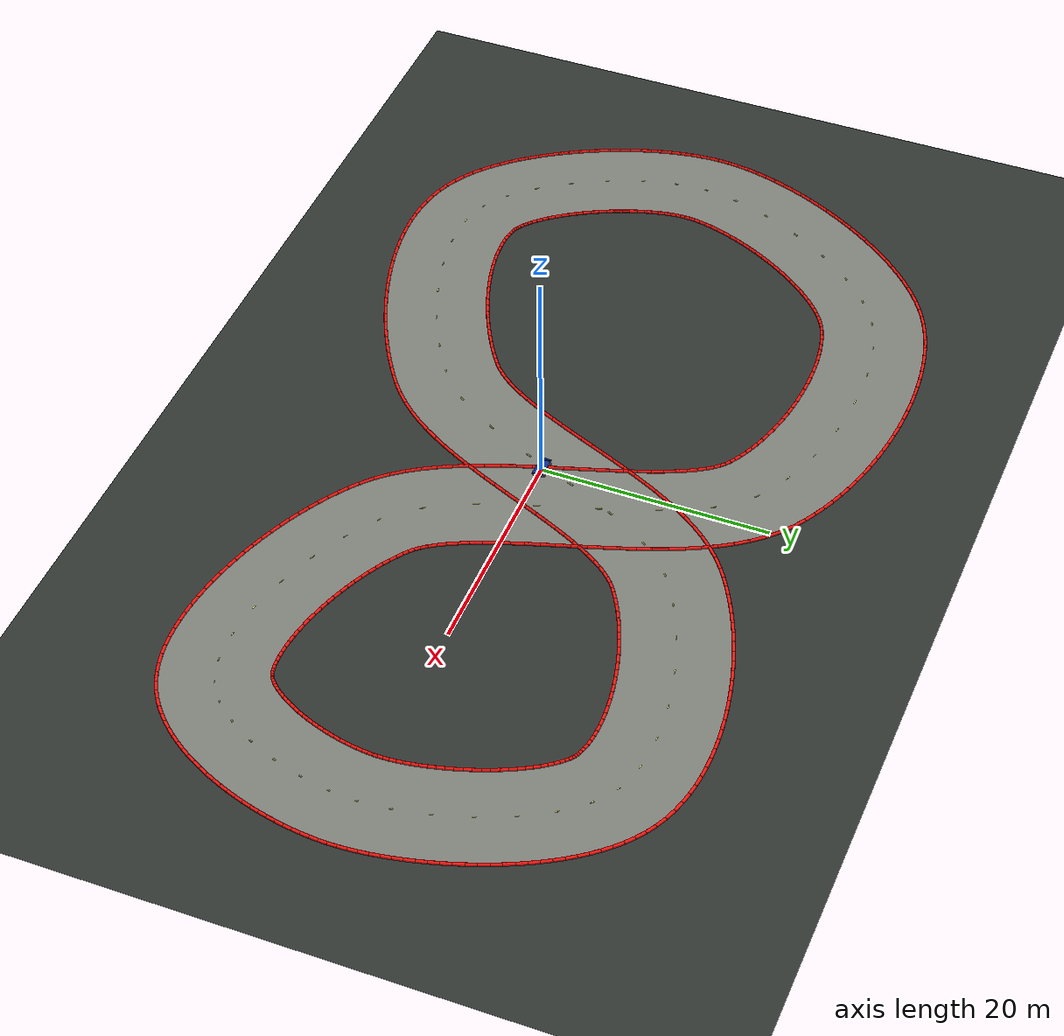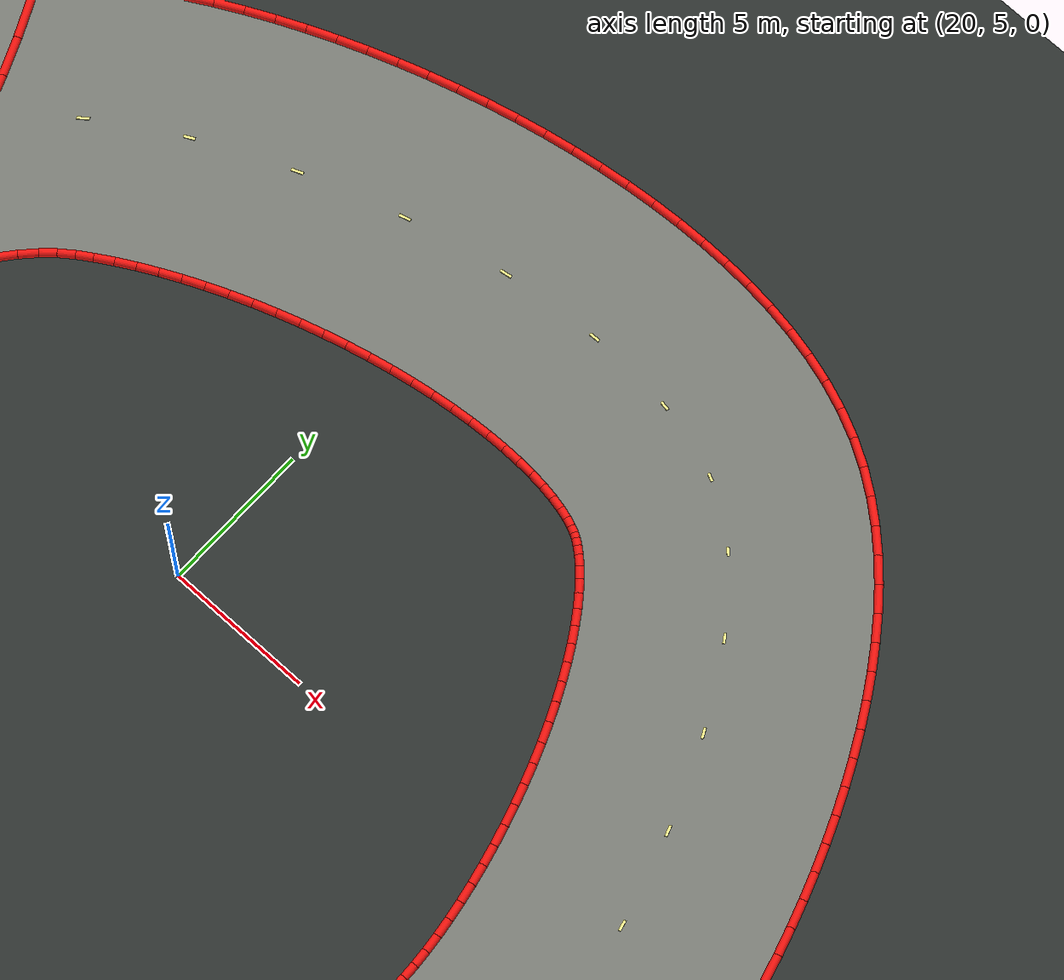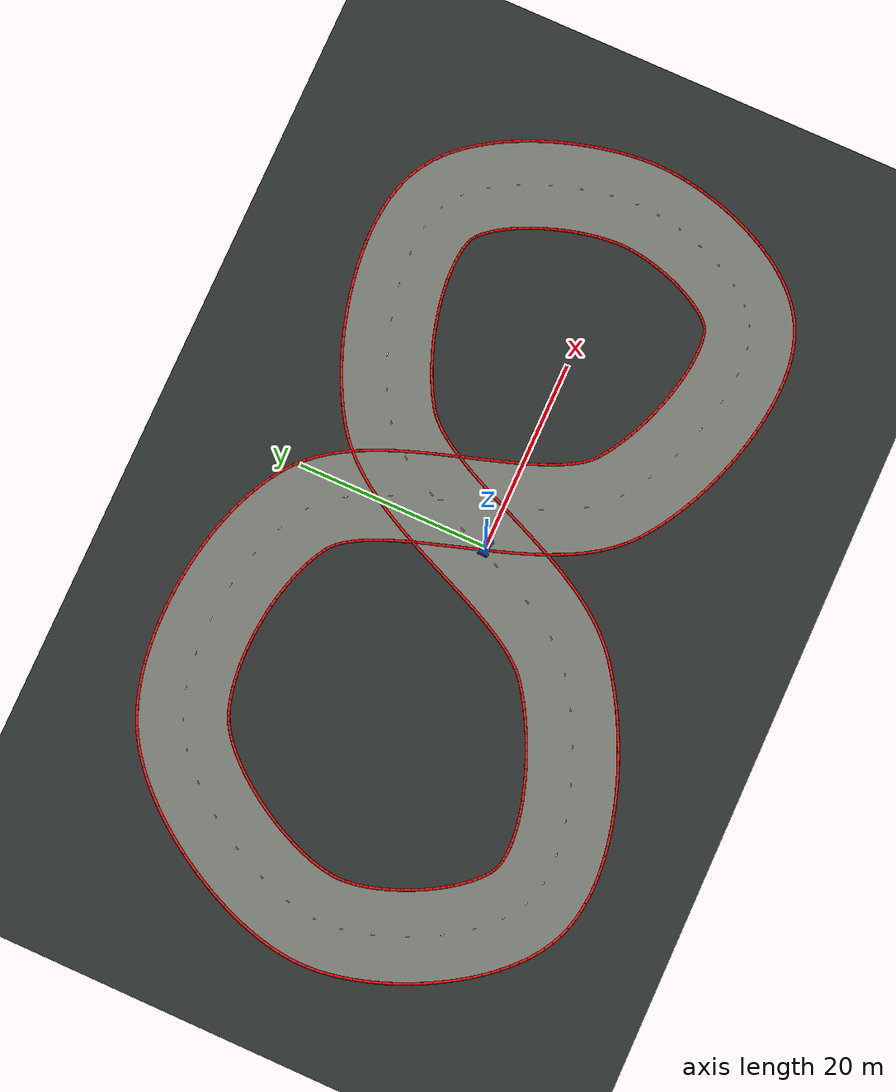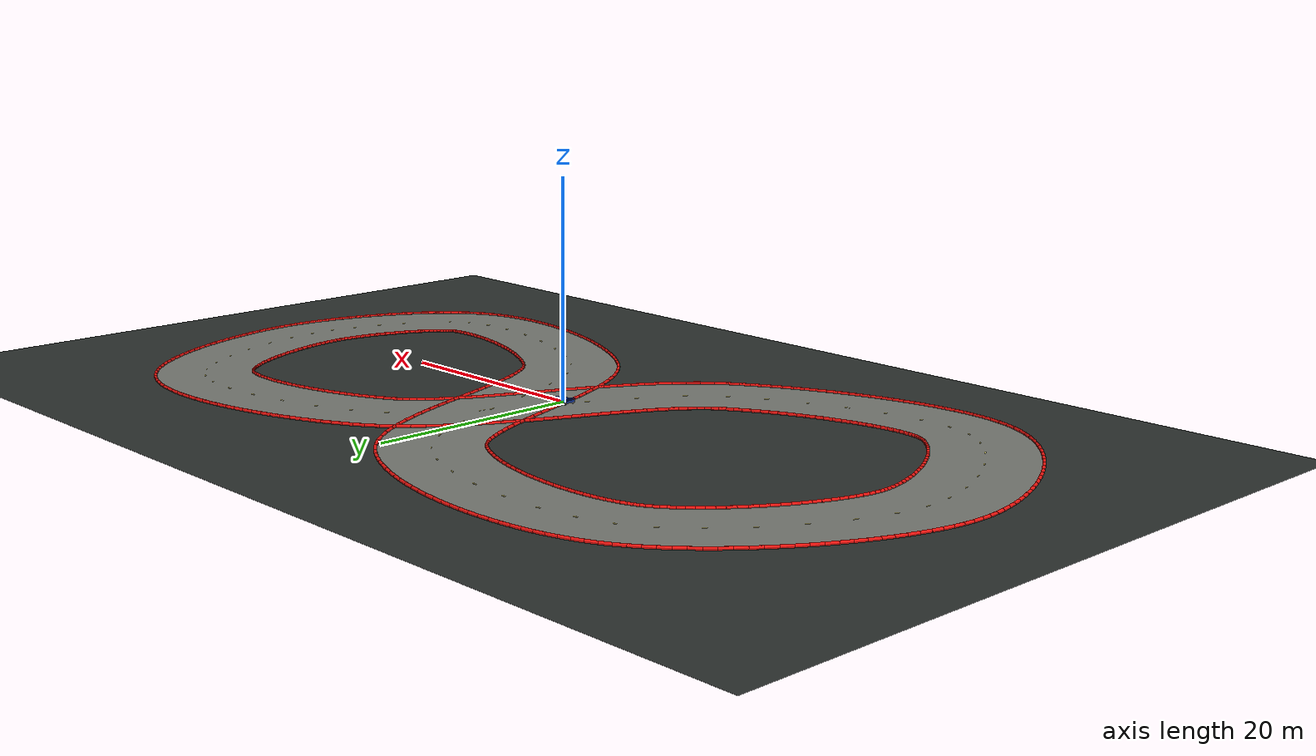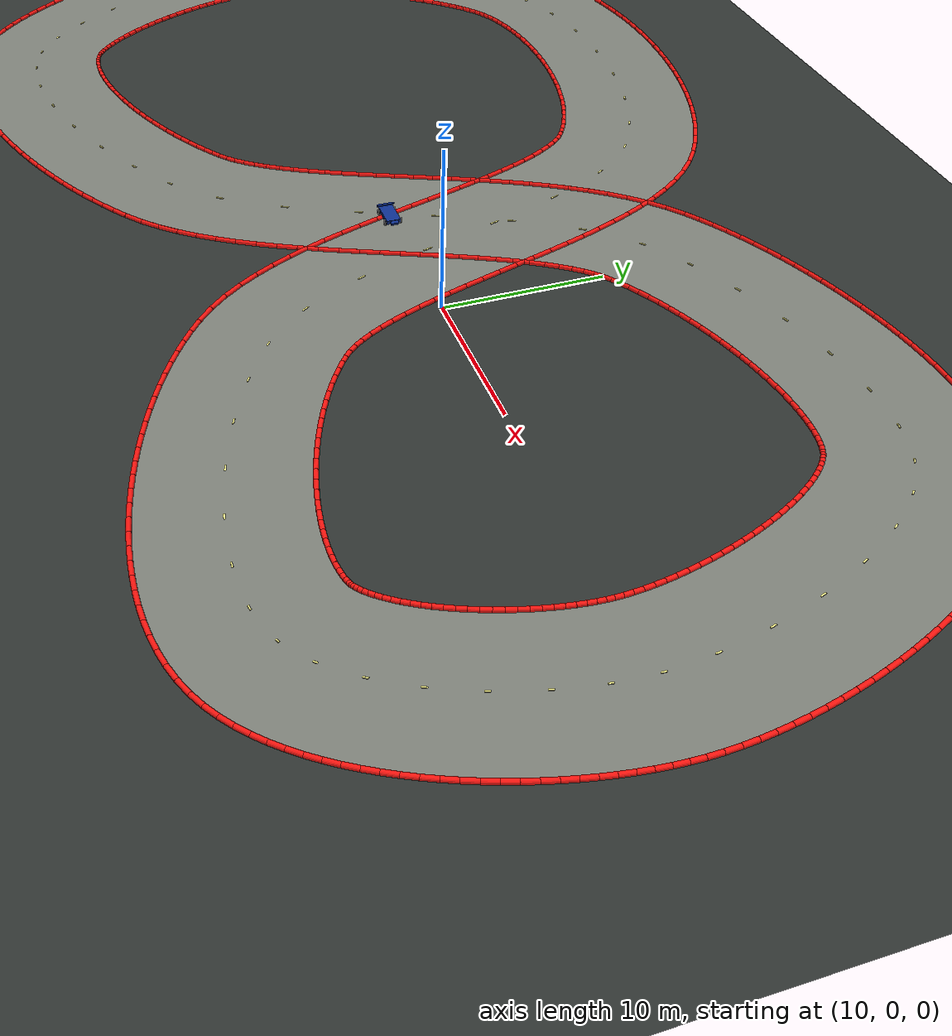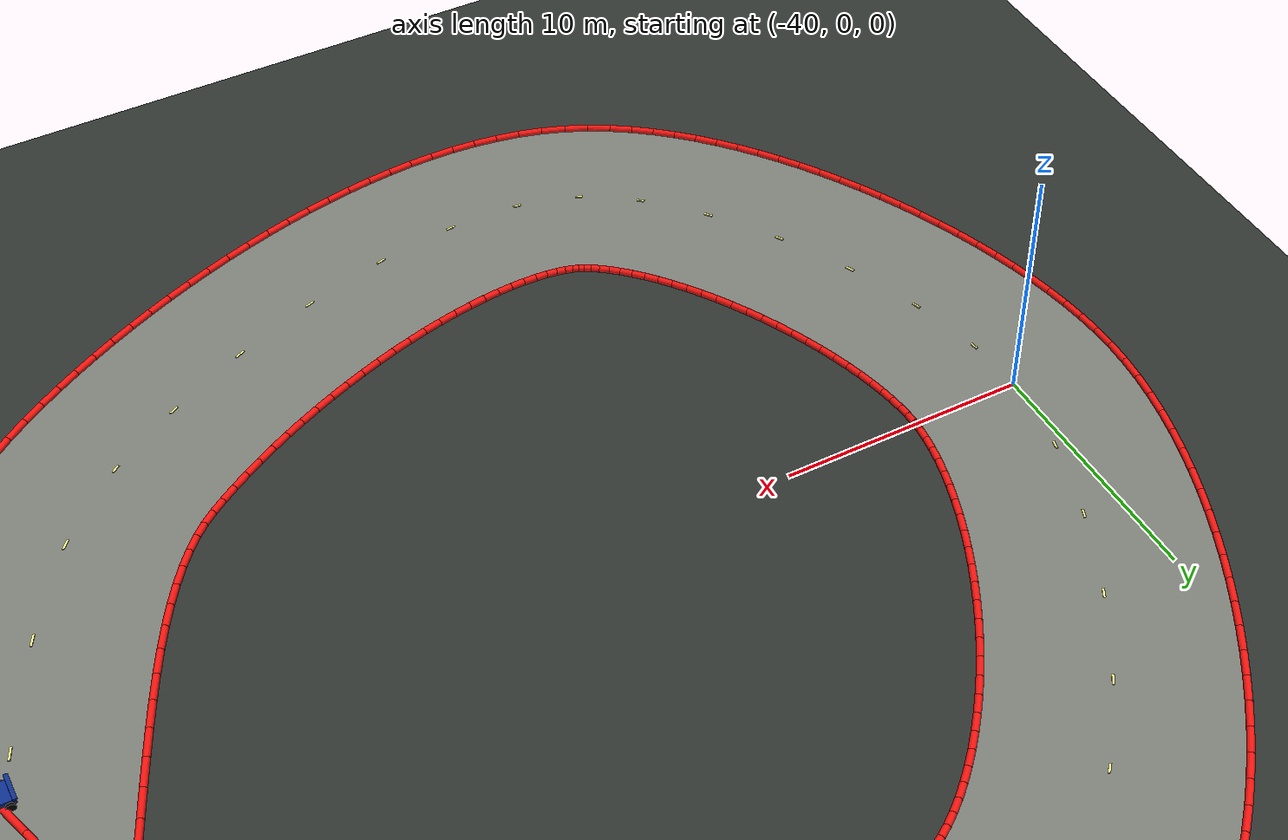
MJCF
<mujoco model="racesim_s_curve_world">
  <compiler angle="degree" autolimits="true"/>
  <option timestep="0.02" gravity="0 0 -9.81"/>
  <visual>
    <global offwidth="1280" offheight="960"/>
    <headlight ambient="0.35 0.35 0.35" diffuse="0.8 0.8 0.8"/>
  </visual>

  <include file="car.xml"/>
  <include file="s_curve_track.xml"/>

  <asset>
    <texture name="grid" type="2d" builtin="checker" width="512" height="512"
             rgb1="0.16 0.18 0.17" rgb2="0.20 0.22 0.21"/>
    <material name="ground" texture="grid" texrepeat="12 12" reflectance="0.05"/>
  </asset>

  <worldbody>
    <light name="sun" pos="0 0 30" dir="0 0 -1" diffuse="1.0 1.0 1.0" ambient="0.25 0.25 0.25"/>
    <geom name="ground" type="plane" size="90 90 0.1" material="ground"/>
    <camera name="topdown" pos="0 0 125" xyaxes="1 0 0 0 1 0" fovy="42"/>
    <camera name="follow" mode="trackcom" target="car" pos="-5 0 3" xyaxes="0 -1 0 0.5 0 0.866"/>
  </worldbody>
</mujoco>

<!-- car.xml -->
<mujoco model="simple_car">
  <default>
    <geom friction="1.2 0.02 0.001" density="600"/>
    <joint damping="0.1"/>
  </default>

  <asset>
    <material name="chassis_blue" rgba="0.05 0.18 0.55 1"/>
    <material name="wheel_dark" rgba="0.02 0.02 0.025 1"/>
  </asset>

  <worldbody>
    <body name="car" pos="0 0 0.28">
      <freejoint name="root"/>
      <geom name="chassis" type="box" size="0.9 0.45 0.12" material="chassis_blue"/>
      <geom name="nose" type="box" pos="0.75 0 0.02" size="0.45 0.25 0.06" material="chassis_blue"/>
      <geom name="rear_wing" type="box" pos="-0.85 0 0.22" size="0.08 0.55 0.04" material="chassis_blue"/>

      <body name="front_left_wheel" pos="0.65 0.48 -0.12">
        <joint name="front_left_spin" type="hinge" axis="0 1 0"/>
        <geom type="cylinder" size="0.18 0.08" euler="90 0 0" material="wheel_dark"/>
      </body>
      <body name="front_right_wheel" pos="0.65 -0.48 -0.12">
        <joint name="front_right_spin" type="hinge" axis="0 1 0"/>
        <geom type="cylinder" size="0.18 0.08" euler="90 0 0" material="wheel_dark"/>
      </body>
      <body name="rear_left_wheel" pos="-0.65 0.48 -0.12">
        <joint name="rear_left_spin" type="hinge" axis="0 1 0"/>
        <geom type="cylinder" size="0.18 0.08" euler="90 0 0" material="wheel_dark"/>
      </body>
      <body name="rear_right_wheel" pos="-0.65 -0.48 -0.12">
        <joint name="rear_right_spin" type="hinge" axis="0 1 0"/>
        <geom type="cylinder" size="0.18 0.08" euler="90 0 0" material="wheel_dark"/>
      </body>
    </body>
  </worldbody>
</mujoco>

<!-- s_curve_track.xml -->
<mujoco model="s_curve_track_visuals">
  <asset>
    <mesh name="track_surface_mesh" inertia="shell" vertex="33.50015 0.03621 0.02200 33.49485 0.48920 0.02200 33.47015 0.98106 0.02200 33.42502 1.51308 0.02200 33.35893 2.07899 0.02200 33.27179 2.67312 0.02200 33.16378 3.29022 0.02200 33.03527 3.92543 0.02200 32.88677 4.57410 0.02200 32.71894 5.23182 0.02200 32.53251 5.89429 0.02200 32.32832 6.55731 0.02200 32.10732 7.21676 0.02200 31.87054 7.86855 0.02200 31.61916 8.50859 0.02200 31.35449 9.13280 0.02200 31.07803 9.73709 0.02200 30.79149 10.31733 0.02200 30.49685 10.86935 0.02200 30.19644 11.38897 0.02200 29.89299 11.87200 0.02200 29.58979 12.31431 0.02200 29.29073 12.71193 0.02200 29.00048 13.06119 0.02200 28.72459 13.35897 0.02200 28.46949 13.60312 0.02200 28.24243 13.79297 0.02200 28.05102 13.93004 0.02200 27.89378 14.02334 0.02200 27.68633 14.12050 0.02200 27.41243 14.22251 0.02200 27.07074 14.32225 0.02200 26.66505 14.41261 0.02200 26.20036 14.48811 0.02200 25.68226 14.54470 0.02200 25.11643 14.57957 0.02200 24.50850 14.59083 0.02200 23.86387 14.57737 0.02200 23.18770 14.53861 0.02200 22.48490 14.47441 0.02200 21.76017 14.38494 0.02200 21.01800 14.27062 0.02200 20.26271 14.13206 0.02200 19.49849 13.97003 0.02200 18.72941 13.78541 0.02200 17.95944 13.57920 0.02200 17.19251 13.35251 0.02200 16.43248 13.10652 0.02200 15.68320 12.84254 0.02200 14.94851 12.56198 0.02200 14.23224 12.26636 0.02200 13.53826 11.95737 0.02200 12.87048 11.63687 0.02200 12.23282 11.30693 0.02200 11.62930 10.96992 0.02200 11.06394 10.62855 0.02200 10.59298 10.32217 0.02200 10.13594 9.97847 0.02200 9.71496 9.59433 0.02200 9.27387 9.12353 0.02200 8.81801 8.56555 0.02200 8.35274 7.92315 0.02200 7.88249 7.20129 0.02200 7.41055 6.40624 0.02200 6.93896 5.54501 0.02200 6.46872 4.62483 0.02200 5.99990 3.65298 0.02200 5.53186 2.63658 0.02200 5.06332 1.58257 0.02200 4.59253 0.49763 0.02200 4.11732 -0.61183 0.02200 3.63512 -1.73967 0.02200 3.14300 -2.88001 0.02200 2.63767 -4.02724 0.02200 2.11546 -5.17604 0.02200 1.57220 -6.32129 0.02200 1.00322 -7.45811 0.02200 0.40316 -8.58179 0.02200 -0.23412 -9.68763 0.02200 -0.91572 -10.77077 0.02200 -1.64985 -11.82586 0.02200 -2.44584 -12.84653 0.02200 -3.31398 -13.82466 0.02200 -4.26495 -14.74943 0.02200 -5.24894 -15.56114 0.02200 -6.07998 -16.16552 0.02200 -6.88495 -16.71370 0.02200 -7.71494 -17.24592 0.02200 -8.56821 -17.76195 0.02200 -9.44297 -18.26135 0.02200 -10.33736 -18.74349 0.02200 -11.24952 -19.20759 0.02200 -12.17756 -19.65277 0.02200 -13.11961 -20.07804 0.02200 -14.07377 -20.48232 0.02200 -15.03823 -20.86446 0.02200 -16.01119 -21.22323 0.02200 -16.99091 -21.55733 0.02200 -17.97576 -21.86538 0.02200 -18.96422 -22.14592 0.02200 -19.95488 -22.39734 0.02200 -20.94650 -22.61793 0.02200 -21.93805 -22.80577 0.02200 -22.92869 -22.95874 0.02200 -23.91785 -23.07436 0.02200 -24.90518 -23.14975 0.02200 -25.89060 -23.18149 0.02200 -26.87423 -23.16542 0.02200 -27.85622 -23.09641 0.02200 -28.83653 -22.96820 0.02200 -29.81445 -22.77312 0.02200 -30.78793 -22.50207 0.02200 -31.74503 -22.14787 0.02200 -32.63550 -21.72675 0.02200 -33.47646 -21.24268 0.02200 -34.26959 -20.70696 0.02200 -35.02057 -20.12655 0.02200 -35.73436 -19.50657 0.02200 -36.41505 -18.85091 0.02200 -37.06583 -18.16268 0.02200 -37.68908 -17.44453 0.02200 -38.28647 -16.69882 0.02200 -38.85913 -15.92780 0.02200 -39.40771 -15.13360 0.02200 -39.93247 -14.31836 0.02200 -40.43341 -13.48416 0.02200 -40.91024 -12.63310 0.02200 -41.36249 -11.76722 0.02200 -41.78952 -10.88857 0.02200 -42.19054 -9.99911 0.02200 -42.56464 -9.10075 0.02200 -42.91076 -8.19529 0.02200 -43.22773 -7.28440 0.02200 -43.51422 -6.36956 0.02200 -43.76872 -5.45206 0.02200 -43.98952 -4.53289 0.02200 -44.17459 -3.61272 0.02200 -44.32151 -2.69183 0.02200 -44.42729 -1.77004 0.02200 -44.48818 -0.84669 0.02200 -44.49932 0.07851 0.02200 -44.45336 1.05286 0.02200 -44.35181 2.03194 0.02200 -44.20031 3.00898 0.02200 -44.00312 3.98507 0.02200 -43.76361 4.96072 0.02200 -43.48453 5.93591 0.02200 -43.16818 6.91016 0.02200 -42.81655 7.88258 0.02200 -42.43142 8.85197 0.02200 -42.01437 9.81685 0.02200 -41.56687 10.77554 0.02200 -41.09028 11.72619 0.02200 -40.58586 12.66681 0.02200 -40.05475 13.59532 0.02200 -39.49800 14.50955 0.02200 -38.91656 15.40728 0.02200 -38.31123 16.28625 0.02200 -37.68264 17.14415 0.02200 -37.03124 17.97867 0.02200 -36.35726 18.78744 0.02200 -35.66060 19.56808 0.02200 -34.94085 20.31810 0.02200 -34.19714 21.03494 0.02200 -33.42809 21.71579 0.02200 -32.63170 22.35753 0.02200 -31.80527 22.95651 0.02200 -30.94540 23.50823 0.02200 -30.05729 24.00219 0.02200 -29.13696 24.43807 0.02200 -28.19458 24.81787 0.02200 -27.23121 25.14729 0.02200 -26.24846 25.43055 0.02200 -25.24776 25.67100 0.02200 -24.23054 25.87131 0.02200 -23.19824 26.03360 0.02200 -22.15245 26.15955 0.02200 -21.09485 26.25047 0.02200 -20.02721 26.30742 0.02200 -18.95146 26.33122 0.02200 -17.86956 26.32249 0.02200 -16.78357 26.28173 0.02200 -15.69562 26.20927 0.02200 -14.60785 26.10532 0.02200 -13.52247 25.97001 0.02200 -12.44165 25.80329 0.02200 -11.36760 25.60505 0.02200 -10.30252 25.37499 0.02200 -9.24857 25.11270 0.02200 -8.20789 24.81757 0.02200 -7.18260 24.48877 0.02200 -6.17481 24.12525 0.02200 -5.18662 23.72561 0.02200 -4.22015 23.28814 0.02200 -3.27765 22.81067 0.02200 -2.36152 22.29053 0.02200 -1.41722 21.68500 0.02200 -0.33796 20.85291 0.02200 0.67784 19.87992 0.02200 1.57544 18.83738 0.02200 2.37093 17.74297 0.02200 3.08057 16.60835 0.02200 3.71903 15.44132 0.02200 4.29881 14.24756 0.02200 4.83035 13.03183 0.02200 5.32239 11.79866 0.02200 5.78230 10.55275 0.02200 6.21638 9.29909 0.02200 6.63018 8.04311 0.02200 7.02857 6.79066 0.02200 7.41597 5.54799 0.02200 7.79632 4.32180 0.02200 8.17319 3.11920 0.02200 8.54973 1.94771 0.02200 8.92863 0.81528 0.02200 9.31206 -0.26973 0.02200 9.70148 -1.29850 0.02200 10.09748 -2.26186 0.02200 10.49948 -3.15031 0.02200 10.90541 -3.95433 0.02200 11.31134 -4.66485 0.02200 11.71115 -5.27405 0.02200 12.09668 -5.77684 0.02200 12.45856 -6.17280 0.02200 12.85555 -6.52209 0.02200 13.26265 -6.82771 0.02200 13.77207 -7.18211 0.02200 14.32234 -7.53517 0.02200 14.90939 -7.88368 0.02200 15.52914 -8.22488 0.02200 16.17752 -8.55637 0.02200 16.85051 -8.87600 0.02200 17.54410 -9.18187 0.02200 18.25429 -9.47226 0.02200 18.97709 -9.74558 0.02200 19.70852 -10.00040 0.02200 20.44454 -10.23538 0.02200 21.18110 -10.44930 0.02200 21.91404 -10.64105 0.02200 22.63912 -10.80961 0.02200 23.35199 -10.95410 0.02200 24.04809 -11.07377 0.02200 24.72270 -11.16809 0.02200 25.37083 -11.23673 0.02200 25.98716 -11.27970 0.02200 26.56607 -11.29745 0.02200 27.10151 -11.29102 0.02200 27.58702 -11.26228 0.02200 28.01583 -11.21425 0.02200 28.38098 -11.15146 0.02200 28.67580 -11.08041 0.02200 28.89471 -11.01004 0.02200 29.04954 -10.94467 0.02200 29.13883 -10.89552 0.02200 29.26641 -10.81173 0.02200 29.42494 -10.69006 0.02200 29.60924 -10.52791 0.02200 29.81390 -10.32444 0.02200 30.03377 -10.08021 0.02200 30.26417 -9.79674 0.02200 30.50102 -9.47623 0.02200 30.74077 -9.12128 0.02200 30.98040 -8.73477 0.02200 31.21732 -8.31969 0.02200 31.44934 -7.87916 0.02200 31.67455 -7.41628 0.02200 31.89133 -6.93419 0.02200 32.09826 -6.43602 0.02200 32.29412 -5.92490 0.02200 32.47783 -5.40393 0.02200 32.64842 -4.87626 0.02200 32.80505 -4.34504 0.02200 32.94699 -3.81344 0.02200 33.07359 -3.28472 0.02200 33.18430 -2.76219 0.02200 33.27868 -2.24927 0.02200 33.35641 -1.74952 0.02200 33.41729 -1.26667 0.02200 33.46134 -0.80469 0.02200 33.48877 -0.36781 0.02200 42.49985 -0.03621 0.02200 42.49060 0.76570 0.02200 42.44987 1.58496 0.02200 42.37980 2.41407 0.02200 42.28202 3.25306 0.02200 42.15774 4.10140 0.02200 42.00789 4.95808 0.02200 41.83321 5.82178 0.02200 41.63430 6.69088 0.02200 41.41163 7.56359 0.02200 41.16556 8.43799 0.02200 40.89637 9.31204 0.02200 40.60423 10.18365 0.02200 40.28921 11.05069 0.02200 39.95124 11.91100 0.02200 39.59013 12.76245 0.02200 39.20549 13.60290 0.02200 38.79672 14.43028 0.02200 38.36295 15.24251 0.02200 37.90297 16.03755 0.02200 37.41515 16.81337 0.02200 36.89733 17.56786 0.02200 36.34672 18.29880 0.02200 35.75975 19.00361 0.02200 35.13200 19.67918 0.02200 34.45814 20.32146 0.02200 33.73204 20.92488 0.02200 32.94721 21.48168 0.02200 32.10622 21.97666 0.02200 31.19453 22.40860 0.02200 30.26472 22.75857 0.02200 29.32399 23.03562 0.02200 28.37447 23.24878 0.02200 27.41704 23.40549 0.02200 26.45202 23.51173 0.02200 25.47961 23.57224 0.02200 24.50008 23.59083 0.02200 23.51393 23.57056 0.02200 22.52188 23.51395 0.02200 21.52492 23.42307 0.02200 20.52425 23.29968 0.02200 19.52127 23.14529 0.02200 18.51754 22.96124 0.02200 17.51479 22.74869 0.02200 16.51484 22.50869 0.02200 15.51960 22.24218 0.02200 14.53104 21.94998 0.02200 13.55119 21.63284 0.02200 12.58210 21.29140 0.02200 11.62583 20.92618 0.02200 10.68443 20.53758 0.02200 9.75994 20.12586 0.02200 8.85433 19.69110 0.02200 7.96958 19.23314 0.02200 7.10757 18.75157 0.02200 6.27016 18.24561 0.02200 5.40702 17.67783 0.02200 4.38631 16.90247 0.02200 3.40316 16.01002 0.02200 2.50810 15.05854 0.02200 1.69016 14.06043 0.02200 0.93835 13.02481 0.02200 0.24260 11.95859 0.02200 -0.40600 10.86735 0.02200 -1.01514 9.75598 0.02200 -1.59142 8.62909 0.02200 -2.14057 7.49130 0.02200 -2.66756 6.34732 0.02200 -3.17676 5.20212 0.02200 -3.67205 4.06087 0.02200 -4.15687 2.92904 0.02200 -4.63430 1.81234 0.02200 -5.10704 0.71678 0.02200 -5.57744 -0.35138 0.02200 -6.04743 -1.38562 0.02200 -6.51851 -2.37915 0.02200 -6.99161 -3.32499 0.02200 -7.46703 -4.21600 0.02200 -7.94424 -5.04499 0.02200 -8.42177 -5.80496 0.02200 -8.89706 -6.48939 0.02200 -9.36640 -7.09278 0.02200 -9.82513 -7.61137 0.02200 -10.26820 -8.04412 0.02200 -10.75106 -8.43886 0.02200 -11.25431 -8.80167 0.02200 -11.84702 -9.20519 0.02200 -12.47282 -9.60637 0.02200 -13.12815 -10.00263 0.02200 -13.80953 -10.39158 0.02200 -14.51351 -10.77105 0.02200 -15.23668 -11.13898 0.02200 -15.97563 -11.49344 0.02200 -16.72696 -11.83262 0.02200 -17.48726 -12.15477 0.02200 -18.25307 -12.45822 0.02200 -19.02091 -12.74139 0.02200 -19.78719 -13.00275 0.02200 -20.54829 -13.24088 0.02200 -21.30044 -13.45442 0.02200 -22.03976 -13.64215 0.02200 -22.76218 -13.80298 0.02200 -23.46347 -13.93599 0.02200 -24.13916 -14.04051 0.02200 -24.78456 -14.11619 0.02200 -25.39471 -14.16308 0.02200 -25.96440 -14.18180 0.02200 -26.48824 -14.17370 0.02200 -26.96079 -14.14107 0.02200 -27.37678 -14.08737 0.02200 -27.73165 -14.01744 0.02200 -28.02217 -13.93757 0.02200 -28.25497 -13.85213 0.02200 -28.45706 -13.75551 0.02200 -28.70430 -13.61205 0.02200 -28.99227 -13.41656 0.02200 -29.31257 -13.16819 0.02200 -29.65750 -12.86791 0.02200 -30.02024 -12.51795 0.02200 -30.39487 -12.12130 0.02200 -30.77630 -11.68141 0.02200 -31.16011 -11.20200 0.02200 -31.54246 -10.68697 0.02200 -31.91996 -10.14025 0.02200 -32.28960 -9.56583 0.02200 -32.64870 -8.96772 0.02200 -32.99477 -8.34994 0.02200 -33.32558 -7.71652 0.02200 -33.63904 -7.07155 0.02200 -33.93319 -6.41915 0.02200 -34.20624 -5.76352 0.02200 -34.45650 -5.10897 0.02200 -34.68242 -4.45993 0.02200 -34.88260 -3.82101 0.02200 -35.05581 -3.19704 0.02200 -35.20104 -2.59312 0.02200 -35.31760 -2.01469 0.02200 -35.40516 -1.46758 0.02200 -35.46399 -0.95807 0.02200 -35.49513 -0.49291 0.02200 -35.50068 -0.07851 0.02200 -35.47903 0.37365 0.02200 -35.42649 0.87492 0.02200 -35.34064 1.42587 0.02200 -35.22044 2.01921 0.02200 -35.06577 2.64824 0.02200 -34.87711 3.30678 0.02200 -34.65539 3.98913 0.02200 -34.40184 4.68998 0.02200 -34.11794 5.40434 0.02200 -33.80531 6.12749 0.02200 -33.46572 6.85492 0.02200 -33.10104 7.58228 0.02200 -32.71326 8.30537 0.02200 -32.30445 9.02007 0.02200 -31.87679 9.72237 0.02200 -31.43257 10.40829 0.02200 -30.97424 11.07390 0.02200 -30.50437 11.71529 0.02200 -30.02575 12.32862 0.02200 -29.54139 12.91003 0.02200 -29.05461 13.45572 0.02200 -28.56907 13.96198 0.02200 -28.08885 14.42519 0.02200 -27.61858 14.84196 0.02200 -27.16348 15.20920 0.02200 -26.72947 15.52439 0.02200 -26.32321 15.78583 0.02200 -25.94271 15.99781 0.02200 -25.53049 16.19226 0.02200 -25.05791 16.38215 0.02200 -24.53016 16.56217 0.02200 -23.95186 16.72850 0.02200 -23.32783 16.87817 0.02200 -22.66291 17.00889 0.02200 -21.96187 17.11893 0.02200 -21.22940 17.20701 0.02200 -20.47005 17.27218 0.02200 -19.68829 17.31381 0.02200 -18.88846 17.33144 0.02200 -18.07482 17.32484 0.02200 -17.25157 17.29391 0.02200 -16.42283 17.23869 0.02200 -15.59269 17.15937 0.02200 -14.76522 17.05622 0.02200 -13.94445 16.92965 0.02200 -13.13445 16.78018 0.02200 -12.33926 16.60849 0.02200 -11.56297 16.41537 0.02200 -10.80967 16.20184 0.02200 -10.08350 15.96910 0.02200 -9.38859 15.71860 0.02200 -8.72910 15.45211 0.02200 -8.10913 15.17175 0.02200 -7.53271 14.88006 0.02200 -7.00366 14.58011 0.02200 -6.58278 14.31500 0.02200 -6.20440 14.02760 0.02200 -5.85939 13.69407 0.02200 -5.48577 13.25712 0.02200 -5.09236 12.71313 0.02200 -4.68816 12.06448 0.02200 -4.28057 11.31744 0.02200 -3.87483 10.48037 0.02200 -3.47412 9.56257 0.02200 -3.07991 8.57356 0.02200 -2.69231 7.52271 0.02200 -2.31036 6.41906 0.02200 -1.93235 5.27125 0.02200 -1.55588 4.08749 0.02200 -1.17811 2.87556 0.02200 -0.79572 1.64283 0.02200 -0.40501 0.39625 0.02200 -0.00187 -0.85766 0.02200 0.41826 -2.11278 0.02200 0.86050 -3.36344 0.02200 1.33063 -4.60438 0.02200 1.83533 -5.83074 0.02200 2.38244 -7.03795 0.02200 2.98130 -8.22147 0.02200 3.64310 -9.37634 0.02200 4.38121 -10.49631 0.02200 5.21108 -11.57241 0.02200 6.14932 -12.59102 0.02200 7.14445 -13.47791 0.02200 7.97194 -14.10840 0.02200 8.76977 -14.66389 0.02200 9.59330 -15.19259 0.02200 10.44047 -15.69577 0.02200 11.30926 -16.17426 0.02200 12.19761 -16.62856 0.02200 13.10344 -17.05888 0.02200 14.02464 -17.46520 0.02200 14.95909 -17.84732 0.02200 15.90466 -18.20491 0.02200 16.85923 -18.53747 0.02200 17.82071 -18.84442 0.02200 18.78705 -19.12505 0.02200 19.75627 -19.37856 0.02200 20.72652 -19.60403 0.02200 21.69603 -19.80044 0.02200 22.66322 -19.96659 0.02200 23.62673 -20.10111 0.02200 24.58542 -20.20239 0.02200 25.53848 -20.26851 0.02200 26.48544 -20.29709 0.02200 27.42623 -20.28516 0.02200 28.36117 -20.22893 0.02200 29.29094 -20.12347 0.02200 30.21637 -19.96232 0.02200 31.13803 -19.73705 0.02200 32.05537 -19.43680 0.02200 32.95046 -19.05533 0.02200 33.73119 -18.63569 0.02200 34.45350 -18.16660 0.02200 35.12389 -17.65583 0.02200 35.74672 -17.11056 0.02200 36.32655 -16.53615 0.02200 36.86768 -15.93662 0.02200 37.37395 -15.31499 0.02200 37.84861 -14.67363 0.02200 38.29436 -14.01447 0.02200 38.71339 -13.33921 0.02200 39.10743 -12.64938 0.02200 39.47786 -11.94645 0.02200 39.82571 -11.23184 0.02200 40.15179 -10.50697 0.02200 40.45665 -9.77328 0.02200 40.74070 -9.03220 0.02200 41.00418 -8.28514 0.02200 41.24719 -7.53354 0.02200 41.46974 -6.77879 0.02200 41.67173 -6.02227 0.02200 41.85296 -5.26529 0.02200 42.01314 -4.50908 0.02200 42.15187 -3.75478 0.02200 42.26864 -3.00337 0.02200 42.36279 -2.25568 0.02200 42.43348 -1.51230 0.02200 42.47962 -0.77354 0.02200" face="0 281 1 0 280 281 1 282 2 1 281 282 2 283 3 2 282 283 3 284 4 3 283 284 4 285 5 4 284 285 5 286 6 5 285 286 6 287 7 6 286 287 7 288 8 7 287 288 8 289 9 8 288 289 9 290 10 9 289 290 10 291 11 10 290 291 11 292 12 11 291 292 12 293 13 12 292 293 13 294 14 13 293 294 14 295 15 14 294 295 15 296 16 15 295 296 16 297 17 16 296 297 17 298 18 17 297 298 18 299 19 18 298 299 19 300 20 19 299 300 20 301 21 20 300 301 21 302 22 21 301 302 22 303 23 22 302 303 23 304 24 23 303 304 24 305 25 24 304 305 25 306 26 25 305 306 26 307 27 26 306 307 27 308 28 27 307 308 28 309 29 28 308 309 29 310 30 29 309 310 30 311 31 30 310 311 31 312 32 31 311 312 32 313 33 32 312 313 33 314 34 33 313 314 34 315 35 34 314 315 35 316 36 35 315 316 36 317 37 36 316 317 37 318 38 37 317 318 38 319 39 38 318 319 39 320 40 39 319 320 40 321 41 40 320 321 41 322 42 41 321 322 42 323 43 42 322 323 43 324 44 43 323 324 44 325 45 44 324 325 45 326 46 45 325 326 46 327 47 46 326 327 47 328 48 47 327 328 48 329 49 48 328 329 49 330 50 49 329 330 50 331 51 50 330 331 51 332 52 51 331 332 52 333 53 52 332 333 53 334 54 53 333 334 54 335 55 54 334 335 55 336 56 55 335 336 56 337 57 56 336 337 57 338 58 57 337 338 58 339 59 58 338 339 59 340 60 59 339 340 60 341 61 60 340 341 61 342 62 61 341 342 62 343 63 62 342 343 63 344 64 63 343 344 64 345 65 64 344 345 65 346 66 65 345 346 66 347 67 66 346 347 67 348 68 67 347 348 68 349 69 68 348 349 69 350 70 69 349 350 70 351 71 70 350 351 71 352 72 71 351 352 72 353 73 72 352 353 73 354 74 73 353 354 74 355 75 74 354 355 75 356 76 75 355 356 76 357 77 76 356 357 77 358 78 77 357 358 78 359 79 78 358 359 79 360 80 79 359 360 80 361 81 80 360 361 81 362 82 81 361 362 82 363 83 82 362 363 83 364 84 83 363 364 84 365 85 84 364 365 85 366 86 85 365 366 86 367 87 86 366 367 87 368 88 87 367 368 88 369 89 88 368 369 89 370 90 89 369 370 90 371 91 90 370 371 91 372 92 91 371 372 92 373 93 92 372 373 93 374 94 93 373 374 94 375 95 94 374 375 95 376 96 95 375 376 96 377 97 96 376 377 97 378 98 97 377 378 98 379 99 98 378 379 99 380 100 99 379 380 100 381 101 100 380 381 101 382 102 101 381 382 102 383 103 102 382 383 103 384 104 103 383 384 104 385 105 104 384 385 105 386 106 105 385 386 106 387 107 106 386 387 107 388 108 107 387 388 108 389 109 108 388 389 109 390 110 109 389 390 110 391 111 110 390 391 111 392 112 111 391 392 112 393 113 112 392 393 113 394 114 113 393 394 114 395 115 114 394 395 115 396 116 115 395 396 116 397 117 116 396 397 117 398 118 117 397 398 118 399 119 118 398 399 119 400 120 119 399 400 120 401 121 120 400 401 121 402 122 121 401 402 122 403 123 122 402 403 123 404 124 123 403 404 124 405 125 124 404 405 125 406 126 125 405 406 126 407 127 126 406 407 127 408 128 127 407 408 128 409 129 128 408 409 129 410 130 129 409 410 130 411 131 130 410 411 131 412 132 131 411 412 132 413 133 132 412 413 133 414 134 133 413 414 134 415 135 134 414 415 135 416 136 135 415 416 136 417 137 136 416 417 137 418 138 137 417 418 138 419 139 138 418 419 139 420 140 139 419 420 140 421 141 140 420 421 141 422 142 141 421 422 142 423 143 142 422 423 143 424 144 143 423 424 144 425 145 144 424 425 145 426 146 145 425 426 146 427 147 146 426 427 147 428 148 147 427 428 148 429 149 148 428 429 149 430 150 149 429 430 150 431 151 150 430 431 151 432 152 151 431 432 152 433 153 152 432 433 153 434 154 153 433 434 154 435 155 154 434 435 155 436 156 155 435 436 156 437 157 156 436 437 157 438 158 157 437 438 158 439 159 158 438 439 159 440 160 159 439 440 160 441 161 160 440 441 161 442 162 161 441 442 162 443 163 162 442 443 163 444 164 163 443 444 164 445 165 164 444 445 165 446 166 165 445 446 166 447 167 166 446 447 167 448 168 167 447 448 168 449 169 168 448 449 169 450 170 169 449 450 170 451 171 170 450 451 171 452 172 171 451 452 172 453 173 172 452 453 173 454 174 173 453 454 174 455 175 174 454 455 175 456 176 175 455 456 176 457 177 176 456 457 177 458 178 177 457 458 178 459 179 178 458 459 179 460 180 179 459 460 180 461 181 180 460 461 181 462 182 181 461 462 182 463 183 182 462 463 183 464 184 183 463 464 184 465 185 184 464 465 185 466 186 185 465 466 186 467 187 186 466 467 187 468 188 187 467 468 188 469 189 188 468 469 189 470 190 189 469 470 190 471 191 190 470 471 191 472 192 191 471 472 192 473 193 192 472 473 193 474 194 193 473 474 194 475 195 194 474 475 195 476 196 195 475 476 196 477 197 196 476 477 197 478 198 197 477 478 198 479 199 198 478 479 199 480 200 199 479 480 200 481 201 200 480 481 201 482 202 201 481 482 202 483 203 202 482 483 203 484 204 203 483 484 204 485 205 204 484 485 205 486 206 205 485 486 206 487 207 206 486 487 207 488 208 207 487 488 208 489 209 208 488 489 209 490 210 209 489 490 210 491 211 210 490 491 211 492 212 211 491 492 212 493 213 212 492 493 213 494 214 213 493 494 214 495 215 214 494 495 215 496 216 215 495 496 216 497 217 216 496 497 217 498 218 217 497 498 218 499 219 218 498 499 219 500 220 219 499 500 220 501 221 220 500 501 221 502 222 221 501 502 222 503 223 222 502 503 223 504 224 223 503 504 224 505 225 224 504 505 225 506 226 225 505 506 226 507 227 226 506 507 227 508 228 227 507 508 228 509 229 228 508 509 229 510 230 229 509 510 230 511 231 230 510 511 231 512 232 231 511 512 232 513 233 232 512 513 233 514 234 233 513 514 234 515 235 234 514 515 235 516 236 235 515 516 236 517 237 236 516 517 237 518 238 237 517 518 238 519 239 238 518 519 239 520 240 239 519 520 240 521 241 240 520 521 241 522 242 241 521 522 242 523 243 242 522 523 243 524 244 243 523 524 244 525 245 244 524 525 245 526 246 245 525 526 246 527 247 246 526 527 247 528 248 247 527 528 248 529 249 248 528 529 249 530 250 249 529 530 250 531 251 250 530 531 251 532 252 251 531 532 252 533 253 252 532 533 253 534 254 253 533 534 254 535 255 254 534 535 255 536 256 255 535 536 256 537 257 256 536 537 257 538 258 257 537 538 258 539 259 258 538 539 259 540 260 259 539 540 260 541 261 260 540 541 261 542 262 261 541 542 262 543 263 262 542 543 263 544 264 263 543 544 264 545 265 264 544 545 265 546 266 265 545 546 266 547 267 266 546 547 267 548 268 267 547 548 268 549 269 268 548 549 269 550 270 269 549 550 270 551 271 270 550 551 271 552 272 271 551 552 272 553 273 272 552 553 273 554 274 273 553 554 274 555 275 274 554 555 275 556 276 275 555 556 276 557 277 276 556 557 277 558 278 277 557 558 278 559 279 278 558 559 279 280 0 279 559 280"/>
    <material name="track_asphalt" rgba="0.48 0.49 0.46 1" emission="0.08"/>
    <material name="track_boundary" rgba="0.95 0.08 0.06 1" emission="0.05"/>
    <material name="track_centerline" rgba="1.0 0.95 0.55 1" emission="0.15"/>
  </asset>
  <worldbody>
    <geom name="track_surface" type="mesh" mesh="track_surface_mesh" material="track_asphalt" contype="0" conaffinity="0"/>
    <geom name="track_left_boundary_000" type="capsule" fromto="33.50015 0.03621 0.09 33.49485 0.48920 0.09" size="0.14" material="track_boundary" contype="0" conaffinity="0"/>
    <geom name="track_left_boundary_001" type="capsule" fromto="33.49485 0.48920 0.09 33.47015 0.98106 0.09" size="0.14" material="track_boundary" contype="0" conaffinity="0"/>
    <geom name="track_left_boundary_002" type="capsule" fromto="33.47015 0.98106 0.09 33.42502 1.51308 0.09" size="0.14" material="track_boundary" contype="0" conaffinity="0"/>
    <geom name="track_left_boundary_003" type="capsule" fromto="33.42502 1.51308 0.09 33.35893 2.07899 0.09" size="0.14" material="track_boundary" contype="0" conaffinity="0"/>
    <geom name="track_left_boundary_004" type="capsule" fromto="33.35893 2.07899 0.09 33.27179 2.67312 0.09" size="0.14" material="track_boundary" contype="0" conaffinity="0"/>
    <geom name="track_left_boundary_005" type="capsule" fromto="33.27179 2.67312 0.09 33.16378 3.29022 0.09" size="0.14" material="track_boundary" contype="0" conaffinity="0"/>
    <geom name="track_left_boundary_006" type="capsule" fromto="33.16378 3.29022 0.09 33.03527 3.92543 0.09" size="0.14" material="track_boundary" contype="0" conaffinity="0"/>
    <geom name="track_left_boundary_007" type="capsule" fromto="33.03527 3.92543 0.09 32.88677 4.57410 0.09" size="0.14" material="track_boundary" contype="0" conaffinity="0"/>
    <geom name="track_left_boundary_008" type="capsule" fromto="32.88677 4.57410 0.09 32.71894 5.23182 0.09" size="0.14" material="track_boundary" contype="0" conaffinity="0"/>
    <geom name="track_left_boundary_009" type="capsule" fromto="32.71894 5.23182 0.09 32.53251 5.89429 0.09" size="0.14" material="track_boundary" contype="0" conaffinity="0"/>
    <geom name="track_left_boundary_010" type="capsule" fromto="32.53251 5.89429 0.09 32.32832 6.55731 0.09" size="0.14" material="track_boundary" contype="0" conaffinity="0"/>
    <geom name="track_left_boundary_011" type="capsule" fromto="32.32832 6.55731 0.09 32.10732 7.21676 0.09" size="0.14" material="track_boundary" contype="0" conaffinity="0"/>
    <geom name="track_left_boundary_012" type="capsule" fromto="32.10732 7.21676 0.09 31.87054 7.86855 0.09" size="0.14" material="track_boundary" contype="0" conaffinity="0"/>
    <geom name="track_left_boundary_013" type="capsule" fromto="31.87054 7.86855 0.09 31.61916 8.50859 0.09" size="0.14" material="track_boundary" contype="0" conaffinity="0"/>
    <geom name="track_left_boundary_014" type="capsule" fromto="31.61916 8.50859 0.09 31.35449 9.13280 0.09" size="0.14" material="track_boundary" contype="0" conaffinity="0"/>
    <geom name="track_left_boundary_015" type="capsule" fromto="31.35449 9.13280 0.09 31.07803 9.73709 0.09" size="0.14" material="track_boundary" contype="0" conaffinity="0"/>
    <geom name="track_left_boundary_016" type="capsule" fromto="31.07803 9.73709 0.09 30.79149 10.31733 0.09" size="0.14" material="track_boundary" contype="0" conaffinity="0"/>
    <geom name="track_left_boundary_017" type="capsule" fromto="30.79149 10.31733 0.09 30.49685 10.86935 0.09" size="0.14" material="track_boundary" contype="0" conaffinity="0"/>
    <geom name="track_left_boundary_018" type="capsule" fromto="30.49685 10.86935 0.09 30.19644 11.38897 0.09" size="0.14" material="track_boundary" contype="0" conaffinity="0"/>
    <geom name="track_left_boundary_019" type="capsule" fromto="30.19644 11.38897 0.09 29.89299 11.87200 0.09" size="0.14" material="track_boundary" contype="0" conaffinity="0"/>
    <geom name="track_left_boundary_020" type="capsule" fromto="29.89299 11.87200 0.09 29.58979 12.31431 0.09" size="0.14" material="track_boundary" contype="0" conaffinity="0"/>
    <geom name="track_left_boundary_021" type="capsule" fromto="29.58979 12.31431 0.09 29.29073 12.71193 0.09" size="0.14" material="track_boundary" contype="0" conaffinity="0"/>
    <geom name="track_left_boundary_022" type="capsule" fromto="29.29073 12.71193 0.09 29.00048 13.06119 0.09" size="0.14" material="track_boundary" contype="0" conaffinity="0"/>
    <geom name="track_left_boundary_023" type="capsule" fromto="29.00048 13.06119 0.09 28.72459 13.35897 0.09" size="0.14" material="track_boundary" contype="0" conaffinity="0"/>
    <geom name="track_left_boundary_024" type="capsule" fromto="28.72459 13.35897 0.09 28.46949 13.60312 0.09" size="0.14" material="track_boundary" contype="0" conaffinity="0"/>
    <geom name="track_left_boundary_025" type="capsule" fromto="28.46949 13.60312 0.09 28.24243 13.79297 0.09" size="0.14" material="track_boundary" contype="0" conaffinity="0"/>
    <geom name="track_left_boundary_026" type="capsule" fromto="28.24243 13.79297 0.09 28.05102 13.93004 0.09" size="0.14" material="track_boundary" contype="0" conaffinity="0"/>
    <geom name="track_left_boundary_027" type="capsule" fromto="28.05102 13.93004 0.09 27.89378 14.02334 0.09" size="0.14" material="track_boundary" contype="0" conaffinity="0"/>
    <geom name="track_left_boundary_028" type="capsule" fromto="27.89378 14.02334 0.09 27.68633 14.12050 0.09" size="0.14" material="track_boundary" contype="0" conaffinity="0"/>
    <geom name="track_left_boundary_029" type="capsule" fromto="27.68633 14.12050 0.09 27.41243 14.22251 0.09" size="0.14" material="track_boundary" contype="0" conaffinity="0"/>
    <geom name="track_left_boundary_030" type="capsule" fromto="27.41243 14.22251 0.09 27.07074 14.32225 0.09" size="0.14" material="track_boundary" contype="0" conaffinity="0"/>
    <geom name="track_left_boundary_031" type="capsule" fromto="27.07074 14.32225 0.09 26.66505 14.41261 0.09" size="0.14" material="track_boundary" contype="0" conaffinity="0"/>
    <geom name="track_left_boundary_032" type="capsule" fromto="26.66505 14.41261 0.09 26.20036 14.48811 0.09" size="0.14" material="track_boundary" contype="0" conaffinity="0"/>
    <geom name="track_left_boundary_033" type="capsule" fromto="26.20036 14.48811 0.09 25.68226 14.54470 0.09" size="0.14" material="track_boundary" contype="0" conaffinity="0"/>
    <geom name="track_left_boundary_034" type="capsule" fromto="25.68226 14.54470 0.09 25.11643 14.57957 0.09" size="0.14" material="track_boundary" contype="0" conaffinity="0"/>
    <geom name="track_left_boundary_035" type="capsule" fromto="25.11643 14.57957 0.09 24.50850 14.59083 0.09" size="0.14" material="track_boundary" contype="0" conaffinity="0"/>
    <geom name="track_left_boundary_036" type="capsule" fromto="24.50850 14.59083 0.09 23.86387 14.57737 0.09" size="0.14" material="track_boundary" contype="0" conaffinity="0"/>
    <geom name="track_left_boundary_037" type="capsule" fromto="23.86387 14.57737 0.09 23.18770 14.53861 0.09" size="0.14" material="track_boundary" contype="0" conaffinity="0"/>
    <geom name="track_left_boundary_038" type="capsule" fromto="23.18770 14.53861 0.09 22.48490 14.47441 0.09" size="0.14" material="track_boundary" contype="0" conaffinity="0"/>
    <geom name="track_left_boundary_039" type="capsule" fromto="22.48490 14.47441 0.09 21.76017 14.38494 0.09" size="0.14" material="track_boundary" contype="0" conaffinity="0"/>
    <geom name="track_left_boundary_040" type="capsule" fromto="21.76017 14.38494 0.09 21.01800 14.27062 0.09" size="0.14" material="track_boundary" contype="0" conaffinity="0"/>
    <geom name="track_left_boundary_041" type="capsule" fromto="21.01800 14.27062 0.09 20.26271 14.13206 0.09" size="0.14" material="track_boundary" contype="0" conaffinity="0"/>
    <geom name="track_left_boundary_042" type="capsule" fromto="20.26271 14.13206 0.09 19.49849 13.97003 0.09" size="0.14" material="track_boundary" contype="0" conaffinity="0"/>
    <geom name="track_left_boundary_043" type="capsule" fromto="19.49849 13.97003 0.09 18.72941 13.78541 0.09" size="0.14" material="track_boundary" contype="0" conaffinity="0"/>
    <geom name="track_left_boundary_044" type="capsule" fromto="18.72941 13.78541 0.09 17.95944 13.57920 0.09" size="0.14" material="track_boundary" contype="0" conaffinity="0"/>
    <geom name="track_left_boundary_045" type="capsule" fromto="17.95944 13.57920 0.09 17.19251 13.35251 0.09" size="0.14" material="track_boundary" contype="0" conaffinity="0"/>
    <geom name="track_left_boundary_046" type="capsule" fromto="17.19251 13.35251 0.09 16.43248 13.10652 0.09" size="0.14" material="track_boundary" contype="0" conaffinity="0"/>
    <geom name="track_left_boundary_047" type="capsule" fromto="16.43248 13.10652 0.09 15.68320 12.84254 0.09" size="0.14" material="track_boundary" contype="0" conaffinity="0"/>
    <geom name="track_left_boundary_048" type="capsule" fromto="15.68320 12.84254 0.09 14.94851 12.56198 0.09" size="0.14" material="track_boundary" contype="0" conaffinity="0"/>
    <geom name="track_left_boundary_049" type="capsule" fromto="14.94851 12.56198 0.09 14.23224 12.26636 0.09" size="0.14" material="track_boundary" contype="0" conaffinity="0"/>
    <geom name="track_left_boundary_050" type="capsule" fromto="14.23224 12.26636 0.09 13.53826 11.95737 0.09" size="0.14" material="track_boundary" contype="0" conaffinity="0"/>
    <geom name="track_left_boundary_051" type="capsule" fromto="13.53826 11.95737 0.09 12.87048 11.63687 0.09" size="0.14" material="track_boundary" contype="0" conaffinity="0"/>
    <geom name="track_left_boundary_052" type="capsule" fromto="12.87048 11.63687 0.09 12.23282 11.30693 0.09" size="0.14" material="track_boundary" contype="0" conaffinity="0"/>
    <geom name="track_left_boundary_053" type="capsule" fromto="12.23282 11.30693 0.09 11.62930 10.96992 0.09" size="0.14" material="track_boundary" contype="0" conaffinity="0"/>
    <geom name="track_left_boundary_054" type="capsule" fromto="11.62930 10.96992 0.09 11.06394 10.62855 0.09" size="0.14" material="track_boundary" contype="0" conaffinity="0"/>
    <geom name="track_left_boundary_055" type="capsule" fromto="11.06394 10.62855 0.09 10.59298 10.32217 0.09" size="0.14" material="track_boundary" contype="0" conaffinity="0"/>
    <geom name="track_left_boundary_056" type="capsule" fromto="10.59298 10.32217 0.09 10.13594 9.97847 0.09" size="0.14" material="track_boundary" contype="0" conaffinity="0"/>
    <geom name="track_left_boundary_057" type="capsule" fromto="10.13594 9.97847 0.09 9.71496 9.59433 0.09" size="0.14" material="track_boundary" contype="0" conaffinity="0"/>
    <geom name="track_left_boundary_058" type="capsule" fromto="9.71496 9.59433 0.09 9.27387 9.12353 0.09" size="0.14" material="track_boundary" contype="0" conaffinity="0"/>
    <geom name="track_left_boundary_059" type="capsule" fromto="9.27387 9.12353 0.09 8.81801 8.56555 0.09" size="0.14" material="track_boundary" contype="0" conaffinity="0"/>
    <geom name="track_left_boundary_060" type="capsule" fromto="8.81801 8.56555 0.09 8.35274 7.92315 0.09" size="0.14" material="track_boundary" contype="0" conaffinity="0"/>
    <geom name="track_left_boundary_061" type="capsule" fromto="8.35274 7.92315 0.09 7.88249 7.20129 0.09" size="0.14" material="track_boundary" contype="0" conaffinity="0"/>
    <geom name="track_left_boundary_062" type="capsule" fromto="7.88249 7.20129 0.09 7.41055 6.40624 0.09" size="0.14" material="track_boundary" contype="0" conaffinity="0"/>
    <geom name="track_left_boundary_063" type="capsule" fromto="7.41055 6.40624 0.09 6.93896 5.54501 0.09" size="0.14" material="track_boundary" contype="0" conaffinity="0"/>
    <geom name="track_left_boundary_064" type="capsule" fromto="6.93896 5.54501 0.09 6.46872 4.62483 0.09" size="0.14" material="track_boundary" contype="0" conaffinity="0"/>
    <geom name="track_left_boundary_065" type="capsule" fromto="6.46872 4.62483 0.09 5.99990 3.65298 0.09" size="0.14" material="track_boundary" contype="0" conaffinity="0"/>
    <geom name="track_left_boundary_066" type="capsule" fromto="5.99990 3.65298 0.09 5.53186 2.63658 0.09" size="0.14" material="track_boundary" contype="0" conaffinity="0"/>
    <geom name="track_left_boundary_067" type="capsule" fromto="5.53186 2.63658 0.09 5.06332 1.58257 0.09" size="0.14" material="track_boundary" contype="0" conaffinity="0"/>
    <geom name="track_left_boundary_068" type="capsule" fromto="5.06332 1.58257 0.09 4.59253 0.49763 0.09" size="0.14" material="track_boundary" contype="0" conaffinity="0"/>
    <geom name="track_left_boundary_069" type="capsule" fromto="4.59253 0.49763 0.09 4.11732 -0.61183 0.09" size="0.14" material="track_boundary" contype="0" conaffinity="0"/>
    <geom name="track_left_boundary_070" type="capsule" fromto="4.11732 -0.61183 0.09 3.63512 -1.73967 0.09" size="0.14" material="track_boundary" contype="0" conaffinity="0"/>
    <geom name="track_left_boundary_071" type="capsule" fromto="3.63512 -1.73967 0.09 3.14300 -2.88001 0.09" size="0.14" material="track_boundary" contype="0" conaffinity="0"/>
    <geom name="track_left_boundary_072" type="capsule" fromto="3.14300 -2.88001 0.09 2.63767 -4.02724 0.09" size="0.14" material="track_boundary" contype="0" conaffinity="0"/>
    <geom name="track_left_boundary_073" type="capsule" fromto="2.63767 -4.02724 0.09 2.11546 -5.17604 0.09" size="0.14" material="track_boundary" contype="0" conaffinity="0"/>
    <geom name="track_left_boundary_074" type="capsule" fromto="2.11546 -5.17604 0.09 1.57220 -6.32129 0.09" size="0.14" material="track_boundary" contype="0" conaffinity="0"/>
    <geom name="track_left_boundary_075" type="capsule" fromto="1.57220 -6.32129 0.09 1.00322 -7.45811 0.09" size="0.14" material="track_boundary" contype="0" conaffinity="0"/>
    <geom name="track_left_boundary_076" type="capsule" fromto="1.00322 -7.45811 0.09 0.40316 -8.58179 0.09" size="0.14" material="track_boundary" contype="0" conaffinity="0"/>
    <geom name="track_left_boundary_077" type="capsule" fromto="0.40316 -8.58179 0.09 -0.23412 -9.68763 0.09" size="0.14" material="track_boundary" contype="0" conaffinity="0"/>
    <geom name="track_left_boundary_078" type="capsule" fromto="-0.23412 -9.68763 0.09 -0.91572 -10.77077 0.09" size="0.14" material="track_boundary" contype="0" conaffinity="0"/>
    <geom name="track_left_boundary_079" type="capsule" fromto="-0.91572 -10.77077 0.09 -1.64985 -11.82586 0.09" size="0.14" material="track_boundary" contype="0" conaffinity="0"/>
    <geom name="track_left_boundary_080" type="capsule" fromto="-1.64985 -11.82586 0.09 -2.44584 -12.84653 0.09" size="0.14" material="track_boundary" contype="0" conaffinity="0"/>
    <geom name="track_left_boundary_081" type="capsule" fromto="-2.44584 -12.84653 0.09 -3.31398 -13.82466 0.09" size="0.14" material="track_boundary" contype="0" conaffinity="0"/>
    <geom name="track_left_boundary_082" type="capsule" fromto="-3.31398 -13.82466 0.09 -4.26495 -14.74943 0.09" size="0.14" material="track_boundary" contype="0" conaffinity="0"/>
    <geom name="track_left_boundary_083" type="capsule" fromto="-4.26495 -14.74943 0.09 -5.24894 -15.56114 0.09" size="0.14" material="track_boundary" contype="0" conaffinity="0"/>
    <geom name="track_left_boundary_084" type="capsule" fromto="-5.24894 -15.56114 0.09 -6.07998 -16.16552 0.09" size="0.14" material="track_boundary" contype="0" conaffinity="0"/>
    <geom name="track_left_boundary_085" type="capsule" fromto="-6.07998 -16.16552 0.09 -6.88495 -16.71370 0.09" size="0.14" material="track_boundary" contype="0" conaffinity="0"/>
    <geom name="track_left_boundary_086" type="capsule" fromto="-6.88495 -16.71370 0.09 -7.71494 -17.24592 0.09" size="0.14" material="track_boundary" contype="0" conaffinity="0"/>
    <geom name="track_left_boundary_087" type="capsule" fromto="-7.71494 -17.24592 0.09 -8.56821 -17.76195 0.09" size="0.14" material="track_boundary" contype="0" conaffinity="0"/>
    <geom name="track_left_boundary_088" type="capsule" fromto="-8.56821 -17.76195 0.09 -9.44297 -18.26135 0.09" size="0.14" material="track_boundary" contype="0" conaffinity="0"/>
    <geom name="track_left_boundary_089" type="capsule" fromto="-9.44297 -18.26135 0.09 -10.33736 -18.74349 0.09" size="0.14" material="track_boundary" contype="0" conaffinity="0"/>
    <geom name="track_left_boundary_090" type="capsule" fromto="-10.33736 -18.74349 0.09 -11.24952 -19.20759 0.09" size="0.14" material="track_boundary" contype="0" conaffinity="0"/>
    <geom name="track_left_boundary_091" type="capsule" fromto="-11.24952 -19.20759 0.09 -12.17756 -19.65277 0.09" size="0.14" material="track_boundary" contype="0" conaffinity="0"/>
    <geom name="track_left_boundary_092" type="capsule" fromto="-12.17756 -19.65277 0.09 -13.11961 -20.07804 0.09" size="0.14" material="track_boundary" contype="0" conaffinity="0"/>
    <geom name="track_left_boundary_093" type="capsule" fromto="-13.11961 -20.07804 0.09 -14.07377 -20.48232 0.09" size="0.14" material="track_boundary" contype="0" conaffinity="0"/>
    <geom name="track_left_boundary_094" type="capsule" fromto="-14.07377 -20.48232 0.09 -15.03823 -20.86446 0.09" size="0.14" material="track_boundary" contype="0" conaffinity="0"/>
    <geom name="track_left_boundary_095" type="capsule" fromto="-15.03823 -20.86446 0.09 -16.01119 -21.22323 0.09" size="0.14" material="track_boundary" contype="0" conaffinity="0"/>
    <geom name="track_left_boundary_096" type="capsule" fromto="-16.01119 -21.22323 0.09 -16.99091 -21.55733 0.09" size="0.14" material="track_boundary" contype="0" conaffinity="0"/>
    <geom name="track_left_boundary_097" type="capsule" fromto="-16.99091 -21.55733 0.09 -17.97576 -21.86538 0.09" size="0.14" material="track_boundary" contype="0" conaffinity="0"/>
    <geom name="track_left_boundary_098" type="capsule" fromto="-17.97576 -21.86538 0.09 -18.96422 -22.14592 0.09" size="0.14" material="track_boundary" contype="0" conaffinity="0"/>
    <geom name="track_left_boundary_099" type="capsule" fromto="-18.96422 -22.14592 0.09 -19.95488 -22.39734 0.09" size="0.14" material="track_boundary" contype="0" conaffinity="0"/>
    <geom name="track_left_boundary_100" type="capsule" fromto="-19.95488 -22.39734 0.09 -20.94650 -22.61793 0.09" size="0.14" material="track_boundary" contype="0" conaffinity="0"/>
    <geom name="track_left_boundary_101" type="capsule" fromto="-20.94650 -22.61793 0.09 -21.93805 -22.80577 0.09" size="0.14" material="track_boundary" contype="0" conaffinity="0"/>
    <geom name="track_left_boundary_102" type="capsule" fromto="-21.93805 -22.80577 0.09 -22.92869 -22.95874 0.09" size="0.14" material="track_boundary" contype="0" conaffinity="0"/>
    <geom name="track_left_boundary_103" type="capsule" fromto="-22.92869 -22.95874 0.09 -23.91785 -23.07436 0.09" size="0.14" material="track_boundary" contype="0" conaffinity="0"/>
    <geom name="track_left_boundary_104" type="capsule" fromto="-23.91785 -23.07436 0.09 -24.90518 -23.14975 0.09" size="0.14" material="track_boundary" contype="0" conaffinity="0"/>
    <geom name="track_left_boundary_105" type="capsule" fromto="-24.90518 -23.14975 0.09 -25.89060 -23.18149 0.09" size="0.14" material="track_boundary" contype="0" conaffinity="0"/>
    <geom name="track_left_boundary_106" type="capsule" fromto="-25.89060 -23.18149 0.09 -26.87423 -23.16542 0.09" size="0.14" material="track_boundary" contype="0" conaffinity="0"/>
    <geom name="track_left_boundary_107" type="capsule" fromto="-26.87423 -23.16542 0.09 -27.85622 -23.09641 0.09" size="0.14" material="track_boundary" contype="0" conaffinity="0"/>
    <geom name="track_left_boundary_108" type="capsule" fromto="-27.85622 -23.09641 0.09 -28.83653 -22.96820 0.09" size="0.14" material="track_boundary" contype="0" conaffinity="0"/>
    <geom name="track_left_boundary_109" type="capsule" fromto="-28.83653 -22.96820 0.09 -29.81445 -22.77312 0.09" size="0.14" material="track_boundary" contype="0" conaffinity="0"/>
    <geom name="track_left_boundary_110" type="capsule" fromto="-29.81445 -22.77312 0.09 -30.78793 -22.50207 0.09" size="0.14" material="track_boundary" contype="0" conaffinity="0"/>
    <geom name="track_left_boundary_111" type="capsule" fromto="-30.78793 -22.50207 0.09 -31.74503 -22.14787 0.09" size="0.14" material="track_boundary" contype="0" conaffinity="0"/>
    <geom name="track_left_boundary_112" type="capsule" fromto="-31.74503 -22.14787 0.09 -32.63550 -21.72675 0.09" size="0.14" material="track_boundary" contype="0" conaffinity="0"/>
    <geom name="track_left_boundary_113" type="capsule" fromto="-32.63550 -21.72675 0.09 -33.47646 -21.24268 0.09" size="0.14" material="track_boundary" contype="0" conaffinity="0"/>
    <geom name="track_left_boundary_114" type="capsule" fromto="-33.47646 -21.24268 0.09 -34.26959 -20.70696 0.09" size="0.14" material="track_boundary" contype="0" conaffinity="0"/>
    <geom name="track_left_boundary_115" type="capsule" fromto="-34.26959 -20.70696 0.09 -35.02057 -20.12655 0.09" size="0.14" material="track_boundary" contype="0" conaffinity="0"/>
    <geom name="track_left_boundary_116" type="capsule" fromto="-35.02057 -20.12655 0.09 -35.73436 -19.50657 0.09" size="0.14" material="track_boundary" contype="0" conaffinity="0"/>
    <geom name="track_left_boundary_117" type="capsule" fromto="-35.73436 -19.50657 0.09 -36.41505 -18.85091 0.09" size="0.14" material="track_boundary" contype="0" conaffinity="0"/>
    <geom name="track_left_boundary_118" type="capsule" fromto="-36.41505 -18.85091 0.09 -37.06583 -18.16268 0.09" size="0.14" material="track_boundary" contype="0" conaffinity="0"/>
    <geom name="track_left_boundary_119" type="capsule" fromto="-37.06583 -18.16268 0.09 -37.68908 -17.44453 0.09" size="0.14" material="track_boundary" contype="0" conaffinity="0"/>
    <geom name="track_left_boundary_120" type="capsule" fromto="-37.68908 -17.44453 0.09 -38.28647 -16.69882 0.09" size="0.14" material="track_boundary" contype="0" conaffinity="0"/>
    <geom name="track_left_boundary_121" type="capsule" fromto="-38.28647 -16.69882 0.09 -38.85913 -15.92780 0.09" size="0.14" material="track_boundary" contype="0" conaffinity="0"/>
    <geom name="track_left_boundary_122" type="capsule" fromto="-38.85913 -15.92780 0.09 -39.40771 -15.13360 0.09" size="0.14" material="track_boundary" contype="0" conaffinity="0"/>
    <geom name="track_left_boundary_123" type="capsule" fromto="-39.40771 -15.13360 0.09 -39.93247 -14.31836 0.09" size="0.14" material="track_boundary" contype="0" conaffinity="0"/>
    <geom name="track_left_boundary_124" type="capsule" fromto="-39.93247 -14.31836 0.09 -40.43341 -13.48416 0.09" size="0.14" material="track_boundary" contype="0" conaffinity="0"/>
    <geom name="track_left_boundary_125" type="capsule" fromto="-40.43341 -13.48416 0.09 -40.91024 -12.63310 0.09" size="0.14" material="track_boundary" contype="0" conaffinity="0"/>
    <geom name="track_left_boundary_126" type="capsule" fromto="-40.91024 -12.63310 0.09 -41.36249 -11.76722 0.09" size="0.14" material="track_boundary" contype="0" conaffinity="0"/>
    <geom name="track_left_boundary_127" type="capsule" fromto="-41.36249 -11.76722 0.09 -41.78952 -10.88857 0.09" size="0.14" material="track_boundary" contype="0" conaffinity="0"/>
    <geom name="track_left_boundary_128" type="capsule" fromto="-41.78952 -10.88857 0.09 -42.19054 -9.99911 0.09" size="0.14" material="track_boundary" contype="0" conaffinity="0"/>
    <geom name="track_left_boundary_129" type="capsule" fromto="-42.19054 -9.99911 0.09 -42.56464 -9.10075 0.09" size="0.14" material="track_boundary" contype="0" conaffinity="0"/>
    <geom name="track_left_boundary_130" type="capsule" fromto="-42.56464 -9.10075 0.09 -42.91076 -8.19529 0.09" size="0.14" material="track_boundary" contype="0" conaffinity="0"/>
    <geom name="track_left_boundary_131" type="capsule" fromto="-42.91076 -8.19529 0.09 -43.22773 -7.28440 0.09" size="0.14" material="track_boundary" contype="0" conaffinity="0"/>
    <geom name="track_left_boundary_132" type="capsule" fromto="-43.22773 -7.28440 0.09 -43.51422 -6.36956 0.09" size="0.14" material="track_boundary" contype="0" conaffinity="0"/>
    <geom name="track_left_boundary_133" type="capsule" fromto="-43.51422 -6.36956 0.09 -43.76872 -5.45206 0.09" size="0.14" material="track_boundary" contype="0" conaffinity="0"/>
    <geom name="track_left_boundary_134" type="capsule" fromto="-43.76872 -5.45206 0.09 -43.98952 -4.53289 0.09" size="0.14" material="track_boundary" contype="0" conaffinity="0"/>
    <geom name="track_left_boundary_135" type="capsule" fromto="-43.98952 -4.53289 0.09 -44.17459 -3.61272 0.09" size="0.14" material="track_boundary" contype="0" conaffinity="0"/>
    <geom name="track_left_boundary_136" type="capsule" fromto="-44.17459 -3.61272 0.09 -44.32151 -2.69183 0.09" size="0.14" material="track_boundary" contype="0" conaffinity="0"/>
    <geom name="track_left_boundary_137" type="capsule" fromto="-44.32151 -2.69183 0.09 -44.42729 -1.77004 0.09" size="0.14" material="track_boundary" contype="0" conaffinity="0"/>
    <geom name="track_left_boundary_138" type="capsule" fromto="-44.42729 -1.77004 0.09 -44.48818 -0.84669 0.09" size="0.14" material="track_boundary" contype="0" conaffinity="0"/>
    <geom name="track_left_boundary_139" type="capsule" fromto="-44.48818 -0.84669 0.09 -44.49932 0.07851 0.09" size="0.14" material="track_boundary" contype="0" conaffinity="0"/>
    <geom name="track_left_boundary_140" type="capsule" fromto="-44.49932 0.07851 0.09 -44.45336 1.05286 0.09" size="0.14" material="track_boundary" contype="0" conaffinity="0"/>
    <geom name="track_left_boundary_141" type="capsule" fromto="-44.45336 1.05286 0.09 -44.35181 2.03194 0.09" size="0.14" material="track_boundary" contype="0" conaffinity="0"/>
    <geom name="track_left_boundary_142" type="capsule" fromto="-44.35181 2.03194 0.09 -44.20031 3.00898 0.09" size="0.14" material="track_boundary" contype="0" conaffinity="0"/>
    <geom name="track_left_boundary_143" type="capsule" fromto="-44.20031 3.00898 0.09 -44.00312 3.98507 0.09" size="0.14" material="track_boundary" contype="0" conaffinity="0"/>
    <geom name="track_left_boundary_144" type="capsule" fromto="-44.00312 3.98507 0.09 -43.76361 4.96072 0.09" size="0.14" material="track_boundary" contype="0" conaffinity="0"/>
    <geom name="track_left_boundary_145" type="capsule" fromto="-43.76361 4.96072 0.09 -43.48453 5.93591 0.09" size="0.14" material="track_boundary" contype="0" conaffinity="0"/>
    <geom name="track_left_boundary_146" type="capsule" fromto="-43.48453 5.93591 0.09 -43.16818 6.91016 0.09" size="0.14" material="track_boundary" contype="0" conaffinity="0"/>
    <geom name="track_left_boundary_147" type="capsule" fromto="-43.16818 6.91016 0.09 -42.81655 7.88258 0.09" size="0.14" material="track_boundary" contype="0" conaffinity="0"/>
    <geom name="track_left_boundary_148" type="capsule" fromto="-42.81655 7.88258 0.09 -42.43142 8.85197 0.09" size="0.14" material="track_boundary" contype="0" conaffinity="0"/>
    <geom name="track_left_boundary_149" type="capsule" fromto="-42.43142 8.85197 0.09 -42.01437 9.81685 0.09" size="0.14" material="track_boundary" contype="0" conaffinity="0"/>
    <geom name="track_left_boundary_150" type="capsule" fromto="-42.01437 9.81685 0.09 -41.56687 10.77554 0.09" size="0.14" material="track_boundary" contype="0" conaffinity="0"/>
    <geom name="track_left_boundary_151" type="capsule" fromto="-41.56687 10.77554 0.09 -41.09028 11.72619 0.09" size="0.14" material="track_boundary" contype="0" conaffinity="0"/>
    <geom name="track_left_boundary_152" type="capsule" fromto="-41.09028 11.72619 0.09 -40.58586 12.66681 0.09" size="0.14" material="track_boundary" contype="0" conaffinity="0"/>
    <geom name="track_left_boundary_153" type="capsule" fromto="-40.58586 12.66681 0.09 -40.05475 13.59532 0.09" size="0.14" material="track_boundary" contype="0" conaffinity="0"/>
    <geom name="track_left_boundary_154" type="capsule" fromto="-40.05475 13.59532 0.09 -39.49800 14.50955 0.09" size="0.14" material="track_boundary" contype="0" conaffinity="0"/>
    <geom name="track_left_boundary_155" type="capsule" fromto="-39.49800 14.50955 0.09 -38.91656 15.40728 0.09" size="0.14" material="track_boundary" contype="0" conaffinity="0"/>
    <geom name="track_left_boundary_156" type="capsule" fromto="-38.91656 15.40728 0.09 -38.31123 16.28625 0.09" size="0.14" material="track_boundary" contype="0" conaffinity="0"/>
    <geom name="track_left_boundary_157" type="capsule" fromto="-38.31123 16.28625 0.09 -37.68264 17.14415 0.09" size="0.14" material="track_boundary" contype="0" conaffinity="0"/>
    <geom name="track_left_boundary_158" type="capsule" fromto="-37.68264 17.14415 0.09 -37.03124 17.97867 0.09" size="0.14" material="track_boundary" contype="0" conaffinity="0"/>
    <geom name="track_left_boundary_159" type="capsule" fromto="-37.03124 17.97867 0.09 -36.35726 18.78744 0.09" size="0.14" material="track_boundary" contype="0" conaffinity="0"/>
    <geom name="track_left_boundary_160" type="capsule" fromto="-36.35726 18.78744 0.09 -35.66060 19.56808 0.09" size="0.14" material="track_boundary" contype="0" conaffinity="0"/>
    <geom name="track_left_boundary_161" type="capsule" fromto="-35.66060 19.56808 0.09 -34.94085 20.31810 0.09" size="0.14" material="track_boundary" contype="0" conaffinity="0"/>
    <geom name="track_left_boundary_162" type="capsule" fromto="-34.94085 20.31810 0.09 -34.19714 21.03494 0.09" size="0.14" material="track_boundary" contype="0" conaffinity="0"/>
    <geom name="track_left_boundary_163" type="capsule" fromto="-34.19714 21.03494 0.09 -33.42809 21.71579 0.09" size="0.14" material="track_boundary" contype="0" conaffinity="0"/>
    <geom name="track_left_boundary_164" type="capsule" fromto="-33.42809 21.71579 0.09 -32.63170 22.35753 0.09" size="0.14" material="track_boundary" contype="0" conaffinity="0"/>
    <geom name="track_left_boundary_165" type="capsule" fromto="-32.63170 22.35753 0.09 -31.80527 22.95651 0.09" size="0.14" material="track_boundary" contype="0" conaffinity="0"/>
    <geom name="track_left_boundary_166" type="capsule" fromto="-31.80527 22.95651 0.09 -30.94540 23.50823 0.09" size="0.14" material="track_boundary" contype="0" conaffinity="0"/>
    <geom name="track_left_boundary_167" type="capsule" fromto="-30.94540 23.50823 0.09 -30.05729 24.00219 0.09" size="0.14" material="track_boundary" contype="0" conaffinity="0"/>
    <geom name="track_left_boundary_168" type="capsule" fromto="-30.05729 24.00219 0.09 -29.13696 24.43807 0.09" size="0.14" material="track_boundary" contype="0" conaffinity="0"/>
    <geom name="track_left_boundary_169" type="capsule" fromto="-29.13696 24.43807 0.09 -28.19458 24.81787 0.09" size="0.14" material="track_boundary" contype="0" conaffinity="0"/>
    <geom name="track_left_boundary_170" type="capsule" fromto="-28.19458 24.81787 0.09 -27.23121 25.14729 0.09" size="0.14" material="track_boundary" contype="0" conaffinity="0"/>
    <geom name="track_left_boundary_171" type="capsule" fromto="-27.23121 25.14729 0.09 -26.24846 25.43055 0.09" size="0.14" material="track_boundary" contype="0" conaffinity="0"/>
    <geom name="track_left_boundary_172" type="capsule" fromto="-26.24846 25.43055 0.09 -25.24776 25.67100 0.09" size="0.14" material="track_boundary" contype="0" conaffinity="0"/>
    <geom name="track_left_boundary_173" type="capsule" fromto="-25.24776 25.67100 0.09 -24.23054 25.87131 0.09" size="0.14" material="track_boundary" contype="0" conaffinity="0"/>
    <geom name="track_left_boundary_174" type="capsule" fromto="-24.23054 25.87131 0.09 -23.19824 26.03360 0.09" size="0.14" material="track_boundary" contype="0" conaffinity="0"/>
    <geom name="track_left_boundary_175" type="capsule" fromto="-23.19824 26.03360 0.09 -22.15245 26.15955 0.09" size="0.14" material="track_boundary" contype="0" conaffinity="0"/>
    <geom name="track_left_boundary_176" type="capsule" fromto="-22.15245 26.15955 0.09 -21.09485 26.25047 0.09" size="0.14" material="track_boundary" contype="0" conaffinity="0"/>
    <geom name="track_left_boundary_177" type="capsule" fromto="-21.09485 26.25047 0.09 -20.02721 26.30742 0.09" size="0.14" material="track_boundary" contype="0" conaffinity="0"/>
    <geom name="track_left_boundary_178" type="capsule" fromto="-20.02721 26.30742 0.09 -18.95146 26.33122 0.09" size="0.14" material="track_boundary" contype="0" conaffinity="0"/>
    <geom name="track_left_boundary_179" type="capsule" fromto="-18.95146 26.33122 0.09 -17.86956 26.32249 0.09" size="0.14" material="track_boundary" contype="0" conaffinity="0"/>
    <geom name="track_left_boundary_180" type="capsule" fromto="-17.86956 26.32249 0.09 -16.78357 26.28173 0.09" size="0.14" material="track_boundary" contype="0" conaffinity="0"/>
    <geom name="track_left_boundary_181" type="capsule" fromto="-16.78357 26.28173 0.09 -15.69562 26.20927 0.09" size="0.14" material="track_boundary" contype="0" conaffinity="0"/>
    <geom name="track_left_boundary_182" type="capsule" fromto="-15.69562 26.20927 0.09 -14.60785 26.10532 0.09" size="0.14" material="track_boundary" contype="0" conaffinity="0"/>
    <geom name="track_left_boundary_183" type="capsule" fromto="-14.60785 26.10532 0.09 -13.52247 25.97001 0.09" size="0.14" material="track_boundary" contype="0" conaffinity="0"/>
    <geom name="track_left_boundary_184" type="capsule" fromto="-13.52247 25.97001 0.09 -12.44165 25.80329 0.09" size="0.14" material="track_boundary" contype="0" conaffinity="0"/>
    <geom name="track_left_boundary_185" type="capsule" fromto="-12.44165 25.80329 0.09 -11.36760 25.60505 0.09" size="0.14" material="track_boundary" contype="0" conaffinity="0"/>
    <geom name="track_left_boundary_186" type="capsule" fromto="-11.36760 25.60505 0.09 -10.30252 25.37499 0.09" size="0.14" material="track_boundary" contype="0" conaffinity="0"/>
    <geom name="track_left_boundary_187" type="capsule" fromto="-10.30252 25.37499 0.09 -9.24857 25.11270 0.09" size="0.14" material="track_boundary" contype="0" conaffinity="0"/>
    <geom name="track_left_boundary_188" type="capsule" fromto="-9.24857 25.11270 0.09 -8.20789 24.81757 0.09" size="0.14" material="track_boundary" contype="0" conaffinity="0"/>
    <geom name="track_left_boundary_189" type="capsule" fromto="-8.20789 24.81757 0.09 -7.18260 24.48877 0.09" size="0.14" material="track_boundary" contype="0" conaffinity="0"/>
    <geom name="track_left_boundary_190" type="capsule" fromto="-7.18260 24.48877 0.09 -6.17481 24.12525 0.09" size="0.14" material="track_boundary" contype="0" conaffinity="0"/>
    <geom name="track_left_boundary_191" type="capsule" fromto="-6.17481 24.12525 0.09 -5.18662 23.72561 0.09" size="0.14" material="track_boundary" contype="0" conaffinity="0"/>
    <geom name="track_left_boundary_192" type="capsule" fromto="-5.18662 23.72561 0.09 -4.22015 23.28814 0.09" size="0.14" material="track_boundary" contype="0" conaffinity="0"/>
    <geom name="track_left_boundary_193" type="capsule" fromto="-4.22015 23.28814 0.09 -3.27765 22.81067 0.09" size="0.14" material="track_boundary" contype="0" conaffinity="0"/>
    <geom name="track_left_boundary_194" type="capsule" fromto="-3.27765 22.81067 0.09 -2.36152 22.29053 0.09" size="0.14" material="track_boundary" contype="0" conaffinity="0"/>
    <geom name="track_left_boundary_195" type="capsule" fromto="-2.36152 22.29053 0.09 -1.41722 21.68500 0.09" size="0.14" material="track_boundary" contype="0" conaffinity="0"/>
    <geom name="track_left_boundary_196" type="capsule" fromto="-1.41722 21.68500 0.09 -0.33796 20.85291 0.09" size="0.14" material="track_boundary" contype="0" conaffinity="0"/>
    <geom name="track_left_boundary_197" type="capsule" fromto="-0.33796 20.85291 0.09 0.67784 19.87992 0.09" size="0.14" material="track_boundary" contype="0" conaffinity="0"/>
    <geom name="track_left_boundary_198" type="capsule" fromto="0.67784 19.87992 0.09 1.57544 18.83738 0.09" size="0.14" material="track_boundary" contype="0" conaffinity="0"/>
    <geom name="track_left_boundary_199" type="capsule" fromto="1.57544 18.83738 0.09 2.37093 17.74297 0.09" size="0.14" material="track_boundary" contype="0" conaffinity="0"/>
    <geom name="track_left_boundary_200" type="capsule" fromto="2.37093 17.74297 0.09 3.08057 16.60835 0.09" size="0.14" material="track_boundary" contype="0" conaffinity="0"/>
    <geom name="track_left_boundary_201" type="capsule" fromto="3.08057 16.60835 0.09 3.71903 15.44132 0.09" size="0.14" material="track_boundary" contype="0" conaffinity="0"/>
    <geom name="track_left_boundary_202" type="capsule" fromto="3.71903 15.44132 0.09 4.29881 14.24756 0.09" size="0.14" material="track_boundary" contype="0" conaffinity="0"/>
    <geom name="track_left_boundary_203" type="capsule" fromto="4.29881 14.24756 0.09 4.83035 13.03183 0.09" size="0.14" material="track_boundary" contype="0" conaffinity="0"/>
    <geom name="track_left_boundary_204" type="capsule" fromto="4.83035 13.03183 0.09 5.32239 11.79866 0.09" size="0.14" material="track_boundary" contype="0" conaffinity="0"/>
    <geom name="track_left_boundary_205" type="capsule" fromto="5.32239 11.79866 0.09 5.78230 10.55275 0.09" size="0.14" material="track_boundary" contype="0" conaffinity="0"/>
    <geom name="track_left_boundary_206" type="capsule" fromto="5.78230 10.55275 0.09 6.21638 9.29909 0.09" size="0.14" material="track_boundary" contype="0" conaffinity="0"/>
    <geom name="track_left_boundary_207" type="capsule" fromto="6.21638 9.29909 0.09 6.63018 8.04311 0.09" size="0.14" material="track_boundary" contype="0" conaffinity="0"/>
    <geom name="track_left_boundary_208" type="capsule" fromto="6.63018 8.04311 0.09 7.02857 6.79066 0.09" size="0.14" material="track_boundary" contype="0" conaffinity="0"/>
    <geom name="track_left_boundary_209" type="capsule" fromto="7.02857 6.79066 0.09 7.41597 5.54799 0.09" size="0.14" material="track_boundary" contype="0" conaffinity="0"/>
    <geom name="track_left_boundary_210" type="capsule" fromto="7.41597 5.54799 0.09 7.79632 4.32180 0.09" size="0.14" material="track_boundary" contype="0" conaffinity="0"/>
    <geom name="track_left_boundary_211" type="capsule" fromto="7.79632 4.32180 0.09 8.17319 3.11920 0.09" size="0.14" material="track_boundary" contype="0" conaffinity="0"/>
    <geom name="track_left_boundary_212" type="capsule" fromto="8.17319 3.11920 0.09 8.54973 1.94771 0.09" size="0.14" material="track_boundary" contype="0" conaffinity="0"/>
    <geom name="track_left_boundary_213" type="capsule" fromto="8.54973 1.94771 0.09 8.92863 0.81528 0.09" size="0.14" material="track_boundary" contype="0" conaffinity="0"/>
    <geom name="track_left_boundary_214" type="capsule" fromto="8.92863 0.81528 0.09 9.31206 -0.26973 0.09" size="0.14" material="track_boundary" contype="0" conaffinity="0"/>
    <geom name="track_left_boundary_215" type="capsule" fromto="9.31206 -0.26973 0.09 9.70148 -1.29850 0.09" size="0.14" material="track_boundary" contype="0" conaffinity="0"/>
    <geom name="track_left_boundary_216" type="capsule" fromto="9.70148 -1.29850 0.09 10.09748 -2.26186 0.09" size="0.14" material="track_boundary" contype="0" conaffinity="0"/>
    <geom name="track_left_boundary_217" type="capsule" fromto="10.09748 -2.26186 0.09 10.49948 -3.15031 0.09" size="0.14" material="track_boundary" contype="0" conaffinity="0"/>
    <geom name="track_left_boundary_218" type="capsule" fromto="10.49948 -3.15031 0.09 10.90541 -3.95433 0.09" size="0.14" material="track_boundary" contype="0" conaffinity="0"/>
    <geom name="track_left_boundary_219" type="capsule" fromto="10.90541 -3.95433 0.09 11.31134 -4.66485 0.09" size="0.14" material="track_boundary" contype="0" conaffinity="0"/>
    <geom name="track_left_boundary_220" type="capsule" fromto="11.31134 -4.66485 0.09 11.71115 -5.27405 0.09" size="0.14" material="track_boundary" contype="0" conaffinity="0"/>
    <geom name="track_left_boundary_221" type="capsule" fromto="11.71115 -5.27405 0.09 12.09668 -5.77684 0.09" size="0.14" material="track_boundary" contype="0" conaffinity="0"/>
    <geom name="track_left_boundary_222" type="capsule" fromto="12.09668 -5.77684 0.09 12.45856 -6.17280 0.09" size="0.14" material="track_boundary" contype="0" conaffinity="0"/>
    <geom name="track_left_boundary_223" type="capsule" fromto="12.45856 -6.17280 0.09 12.85555 -6.52209 0.09" size="0.14" material="track_boundary" contype="0" conaffinity="0"/>
    <geom name="track_left_boundary_224" type="capsule" fromto="12.85555 -6.52209 0.09 13.26265 -6.82771 0.09" size="0.14" material="track_boundary" contype="0" conaffinity="0"/>
    <geom name="track_left_boundary_225" type="capsule" fromto="13.26265 -6.82771 0.09 13.77207 -7.18211 0.09" size="0.14" material="track_boundary" contype="0" conaffinity="0"/>
    <geom name="track_left_boundary_226" type="capsule" fromto="13.77207 -7.18211 0.09 14.32234 -7.53517 0.09" size="0.14" material="track_boundary" contype="0" conaffinity="0"/>
    <geom name="track_left_boundary_227" type="capsule" fromto="14.32234 -7.53517 0.09 14.90939 -7.88368 0.09" size="0.14" material="track_boundary" contype="0" conaffinity="0"/>
    <geom name="track_left_boundary_228" type="capsule" fromto="14.90939 -7.88368 0.09 15.52914 -8.22488 0.09" size="0.14" material="track_boundary" contype="0" conaffinity="0"/>
    <geom name="track_left_boundary_229" type="capsule" fromto="15.52914 -8.22488 0.09 16.17752 -8.55637 0.09" size="0.14" material="track_boundary" contype="0" conaffinity="0"/>
    <geom name="track_left_boundary_230" type="capsule" fromto="16.17752 -8.55637 0.09 16.85051 -8.87600 0.09" size="0.14" material="track_boundary" contype="0" conaffinity="0"/>
    <geom name="track_left_boundary_231" type="capsule" fromto="16.85051 -8.87600 0.09 17.54410 -9.18187 0.09" size="0.14" material="track_boundary" contype="0" conaffinity="0"/>
    <geom name="track_left_boundary_232" type="capsule" fromto="17.54410 -9.18187 0.09 18.25429 -9.47226 0.09" size="0.14" material="track_boundary" contype="0" conaffinity="0"/>
    <geom name="track_left_boundary_233" type="capsule" fromto="18.25429 -9.47226 0.09 18.97709 -9.74558 0.09" size="0.14" material="track_boundary" contype="0" conaffinity="0"/>
    <geom name="track_left_boundary_234" type="capsule" fromto="18.97709 -9.74558 0.09 19.70852 -10.00040 0.09" size="0.14" material="track_boundary" contype="0" conaffinity="0"/>
    <geom name="track_left_boundary_235" type="capsule" fromto="19.70852 -10.00040 0.09 20.44454 -10.23538 0.09" size="0.14" material="track_boundary" contype="0" conaffinity="0"/>
    <geom name="track_left_boundary_236" type="capsule" fromto="20.44454 -10.23538 0.09 21.18110 -10.44930 0.09" size="0.14" material="track_boundary" contype="0" conaffinity="0"/>
    <geom name="track_left_boundary_237" type="capsule" fromto="21.18110 -10.44930 0.09 21.91404 -10.64105 0.09" size="0.14" material="track_boundary" contype="0" conaffinity="0"/>
    <geom name="track_left_boundary_238" type="capsule" fromto="21.91404 -10.64105 0.09 22.63912 -10.80961 0.09" size="0.14" material="track_boundary" contype="0" conaffinity="0"/>
    <geom name="track_left_boundary_239" type="capsule" fromto="22.63912 -10.80961 0.09 23.35199 -10.95410 0.09" size="0.14" material="track_boundary" contype="0" conaffinity="0"/>
    <geom name="track_left_boundary_240" type="capsule" fromto="23.35199 -10.95410 0.09 24.04809 -11.07377 0.09" size="0.14" material="track_boundary" contype="0" conaffinity="0"/>
    <geom name="track_left_boundary_241" type="capsule" fromto="24.04809 -11.07377 0.09 24.72270 -11.16809 0.09" size="0.14" material="track_boundary" contype="0" conaffinity="0"/>
    <geom name="track_left_boundary_242" type="capsule" fromto="24.72270 -11.16809 0.09 25.37083 -11.23673 0.09" size="0.14" material="track_boundary" contype="0" conaffinity="0"/>
    <geom name="track_left_boundary_243" type="capsule" fromto="25.37083 -11.23673 0.09 25.98716 -11.27970 0.09" size="0.14" material="track_boundary" contype="0" conaffinity="0"/>
    <geom name="track_left_boundary_244" type="capsule" fromto="25.98716 -11.27970 0.09 26.56607 -11.29745 0.09" size="0.14" material="track_boundary" contype="0" conaffinity="0"/>
    <geom name="track_left_boundary_245" type="capsule" fromto="26.56607 -11.29745 0.09 27.10151 -11.29102 0.09" size="0.14" material="track_boundary" contype="0" conaffinity="0"/>
    <geom name="track_left_boundary_246" type="capsule" fromto="27.10151 -11.29102 0.09 27.58702 -11.26228 0.09" size="0.14" material="track_boundary" contype="0" conaffinity="0"/>
    <geom name="track_left_boundary_247" type="capsule" fromto="27.58702 -11.26228 0.09 28.01583 -11.21425 0.09" size="0.14" material="track_boundary" contype="0" conaffinity="0"/>
    <geom name="track_left_boundary_248" type="capsule" fromto="28.01583 -11.21425 0.09 28.38098 -11.15146 0.09" size="0.14" material="track_boundary" contype="0" conaffinity="0"/>
    <geom name="track_left_boundary_249" type="capsule" fromto="28.38098 -11.15146 0.09 28.67580 -11.08041 0.09" size="0.14" material="track_boundary" contype="0" conaffinity="0"/>
    <geom name="track_left_boundary_250" type="capsule" fromto="28.67580 -11.08041 0.09 28.89471 -11.01004 0.09" size="0.14" material="track_boundary" contype="0" conaffinity="0"/>
    <geom name="track_left_boundary_251" type="capsule" fromto="28.89471 -11.01004 0.09 29.04954 -10.94467 0.09" size="0.14" material="track_boundary" contype="0" conaffinity="0"/>
    <geom name="track_left_boundary_252" type="capsule" fromto="29.04954 -10.94467 0.09 29.13883 -10.89552 0.09" size="0.14" material="track_boundary" contype="0" conaffinity="0"/>
    <geom name="track_left_boundary_253" type="capsule" fromto="29.13883 -10.89552 0.09 29.26641 -10.81173 0.09" size="0.14" material="track_boundary" contype="0" conaffinity="0"/>
    <geom name="track_left_boundary_254" type="capsule" fromto="29.26641 -10.81173 0.09 29.42494 -10.69006 0.09" size="0.14" material="track_boundary" contype="0" conaffinity="0"/>
    <geom name="track_left_boundary_255" type="capsule" fromto="29.42494 -10.69006 0.09 29.60924 -10.52791 0.09" size="0.14" material="track_boundary" contype="0" conaffinity="0"/>
    <geom name="track_left_boundary_256" type="capsule" fromto="29.60924 -10.52791 0.09 29.81390 -10.32444 0.09" size="0.14" material="track_boundary" contype="0" conaffinity="0"/>
    <geom name="track_left_boundary_257" type="capsule" fromto="29.81390 -10.32444 0.09 30.03377 -10.08021 0.09" size="0.14" material="track_boundary" contype="0" conaffinity="0"/>
    <geom name="track_left_boundary_258" type="capsule" fromto="30.03377 -10.08021 0.09 30.26417 -9.79674 0.09" size="0.14" material="track_boundary" contype="0" conaffinity="0"/>
    <geom name="track_left_boundary_259" type="capsule" fromto="30.26417 -9.79674 0.09 30.50102 -9.47623 0.09" size="0.14" material="track_boundary" contype="0" conaffinity="0"/>
    <geom name="track_left_boundary_260" type="capsule" fromto="30.50102 -9.47623 0.09 30.74077 -9.12128 0.09" size="0.14" material="track_boundary" contype="0" conaffinity="0"/>
    <geom name="track_left_boundary_261" type="capsule" fromto="30.74077 -9.12128 0.09 30.98040 -8.73477 0.09" size="0.14" material="track_boundary" contype="0" conaffinity="0"/>
    <geom name="track_left_boundary_262" type="capsule" fromto="30.98040 -8.73477 0.09 31.21732 -8.31969 0.09" size="0.14" material="track_boundary" contype="0" conaffinity="0"/>
    <geom name="track_left_boundary_263" type="capsule" fromto="31.21732 -8.31969 0.09 31.44934 -7.87916 0.09" size="0.14" material="track_boundary" contype="0" conaffinity="0"/>
    <geom name="track_left_boundary_264" type="capsule" fromto="31.44934 -7.87916 0.09 31.67455 -7.41628 0.09" size="0.14" material="track_boundary" contype="0" conaffinity="0"/>
    <geom name="track_left_boundary_265" type="capsule" fromto="31.67455 -7.41628 0.09 31.89133 -6.93419 0.09" size="0.14" material="track_boundary" contype="0" conaffinity="0"/>
    <geom name="track_left_boundary_266" type="capsule" fromto="31.89133 -6.93419 0.09 32.09826 -6.43602 0.09" size="0.14" material="track_boundary" contype="0" conaffinity="0"/>
    <geom name="track_left_boundary_267" type="capsule" fromto="32.09826 -6.43602 0.09 32.29412 -5.92490 0.09" size="0.14" material="track_boundary" contype="0" conaffinity="0"/>
    <geom name="track_left_boundary_268" type="capsule" fromto="32.29412 -5.92490 0.09 32.47783 -5.40393 0.09" size="0.14" material="track_boundary" contype="0" conaffinity="0"/>
    <geom name="track_left_boundary_269" type="capsule" fromto="32.47783 -5.40393 0.09 32.64842 -4.87626 0.09" size="0.14" material="track_boundary" contype="0" conaffinity="0"/>
    <geom name="track_left_boundary_270" type="capsule" fromto="32.64842 -4.87626 0.09 32.80505 -4.34504 0.09" size="0.14" material="track_boundary" contype="0" conaffinity="0"/>
    <geom name="track_left_boundary_271" type="capsule" fromto="32.80505 -4.34504 0.09 32.94699 -3.81344 0.09" size="0.14" material="track_boundary" contype="0" conaffinity="0"/>
    <geom name="track_left_boundary_272" type="capsule" fromto="32.94699 -3.81344 0.09 33.07359 -3.28472 0.09" size="0.14" material="track_boundary" contype="0" conaffinity="0"/>
    <geom name="track_left_boundary_273" type="capsule" fromto="33.07359 -3.28472 0.09 33.18430 -2.76219 0.09" size="0.14" material="track_boundary" contype="0" conaffinity="0"/>
    <geom name="track_left_boundary_274" type="capsule" fromto="33.18430 -2.76219 0.09 33.27868 -2.24927 0.09" size="0.14" material="track_boundary" contype="0" conaffinity="0"/>
    <geom name="track_left_boundary_275" type="capsule" fromto="33.27868 -2.24927 0.09 33.35641 -1.74952 0.09" size="0.14" material="track_boundary" contype="0" conaffinity="0"/>
    <geom name="track_left_boundary_276" type="capsule" fromto="33.35641 -1.74952 0.09 33.41729 -1.26667 0.09" size="0.14" material="track_boundary" contype="0" conaffinity="0"/>
    <geom name="track_left_boundary_277" type="capsule" fromto="33.41729 -1.26667 0.09 33.46134 -0.80469 0.09" size="0.14" material="track_boundary" contype="0" conaffinity="0"/>
    <geom name="track_left_boundary_278" type="capsule" fromto="33.46134 -0.80469 0.09 33.48877 -0.36781 0.09" size="0.14" material="track_boundary" contype="0" conaffinity="0"/>
    <geom name="track_left_boundary_279" type="capsule" fromto="33.48877 -0.36781 0.09 33.50015 0.03621 0.09" size="0.14" material="track_boundary" contype="0" conaffinity="0"/>
    <geom name="track_right_boundary_000" type="capsule" fromto="42.49985 -0.03621 0.09 42.49060 0.76570 0.09" size="0.14" material="track_boundary" contype="0" conaffinity="0"/>
    <geom name="track_right_boundary_001" type="capsule" fromto="42.49060 0.76570 0.09 42.44987 1.58496 0.09" size="0.14" material="track_boundary" contype="0" conaffinity="0"/>
    <geom name="track_right_boundary_002" type="capsule" fromto="42.44987 1.58496 0.09 42.37980 2.41407 0.09" size="0.14" material="track_boundary" contype="0" conaffinity="0"/>
    <geom name="track_right_boundary_003" type="capsule" fromto="42.37980 2.41407 0.09 42.28202 3.25306 0.09" size="0.14" material="track_boundary" contype="0" conaffinity="0"/>
    <geom name="track_right_boundary_004" type="capsule" fromto="42.28202 3.25306 0.09 42.15774 4.10140 0.09" size="0.14" material="track_boundary" contype="0" conaffinity="0"/>
    <geom name="track_right_boundary_005" type="capsule" fromto="42.15774 4.10140 0.09 42.00789 4.95808 0.09" size="0.14" material="track_boundary" contype="0" conaffinity="0"/>
    <geom name="track_right_boundary_006" type="capsule" fromto="42.00789 4.95808 0.09 41.83321 5.82178 0.09" size="0.14" material="track_boundary" contype="0" conaffinity="0"/>
    <geom name="track_right_boundary_007" type="capsule" fromto="41.83321 5.82178 0.09 41.63430 6.69088 0.09" size="0.14" material="track_boundary" contype="0" conaffinity="0"/>
    <geom name="track_right_boundary_008" type="capsule" fromto="41.63430 6.69088 0.09 41.41163 7.56359 0.09" size="0.14" material="track_boundary" contype="0" conaffinity="0"/>
    <geom name="track_right_boundary_009" type="capsule" fromto="41.41163 7.56359 0.09 41.16556 8.43799 0.09" size="0.14" material="track_boundary" contype="0" conaffinity="0"/>
    <geom name="track_right_boundary_010" type="capsule" fromto="41.16556 8.43799 0.09 40.89637 9.31204 0.09" size="0.14" material="track_boundary" contype="0" conaffinity="0"/>
    <geom name="track_right_boundary_011" type="capsule" fromto="40.89637 9.31204 0.09 40.60423 10.18365 0.09" size="0.14" material="track_boundary" contype="0" conaffinity="0"/>
    <geom name="track_right_boundary_012" type="capsule" fromto="40.60423 10.18365 0.09 40.28921 11.05069 0.09" size="0.14" material="track_boundary" contype="0" conaffinity="0"/>
    <geom name="track_right_boundary_013" type="capsule" fromto="40.28921 11.05069 0.09 39.95124 11.91100 0.09" size="0.14" material="track_boundary" contype="0" conaffinity="0"/>
    <geom name="track_right_boundary_014" type="capsule" fromto="39.95124 11.91100 0.09 39.59013 12.76245 0.09" size="0.14" material="track_boundary" contype="0" conaffinity="0"/>
    <geom name="track_right_boundary_015" type="capsule" fromto="39.59013 12.76245 0.09 39.20549 13.60290 0.09" size="0.14" material="track_boundary" contype="0" conaffinity="0"/>
    <geom name="track_right_boundary_016" type="capsule" fromto="39.20549 13.60290 0.09 38.79672 14.43028 0.09" size="0.14" material="track_boundary" contype="0" conaffinity="0"/>
    <geom name="track_right_boundary_017" type="capsule" fromto="38.79672 14.43028 0.09 38.36295 15.24251 0.09" size="0.14" material="track_boundary" contype="0" conaffinity="0"/>
    <geom name="track_right_boundary_018" type="capsule" fromto="38.36295 15.24251 0.09 37.90297 16.03755 0.09" size="0.14" material="track_boundary" contype="0" conaffinity="0"/>
    <geom name="track_right_boundary_019" type="capsule" fromto="37.90297 16.03755 0.09 37.41515 16.81337 0.09" size="0.14" material="track_boundary" contype="0" conaffinity="0"/>
    <geom name="track_right_boundary_020" type="capsule" fromto="37.41515 16.81337 0.09 36.89733 17.56786 0.09" size="0.14" material="track_boundary" contype="0" conaffinity="0"/>
    <geom name="track_right_boundary_021" type="capsule" fromto="36.89733 17.56786 0.09 36.34672 18.29880 0.09" size="0.14" material="track_boundary" contype="0" conaffinity="0"/>
    <geom name="track_right_boundary_022" type="capsule" fromto="36.34672 18.29880 0.09 35.75975 19.00361 0.09" size="0.14" material="track_boundary" contype="0" conaffinity="0"/>
    <geom name="track_right_boundary_023" type="capsule" fromto="35.75975 19.00361 0.09 35.13200 19.67918 0.09" size="0.14" material="track_boundary" contype="0" conaffinity="0"/>
    <geom name="track_right_boundary_024" type="capsule" fromto="35.13200 19.67918 0.09 34.45814 20.32146 0.09" size="0.14" material="track_boundary" contype="0" conaffinity="0"/>
    <geom name="track_right_boundary_025" type="capsule" fromto="34.45814 20.32146 0.09 33.73204 20.92488 0.09" size="0.14" material="track_boundary" contype="0" conaffinity="0"/>
    <geom name="track_right_boundary_026" type="capsule" fromto="33.73204 20.92488 0.09 32.94721 21.48168 0.09" size="0.14" material="track_boundary" contype="0" conaffinity="0"/>
    <geom name="track_right_boundary_027" type="capsule" fromto="32.94721 21.48168 0.09 32.10622 21.97666 0.09" size="0.14" material="track_boundary" contype="0" conaffinity="0"/>
    <geom name="track_right_boundary_028" type="capsule" fromto="32.10622 21.97666 0.09 31.19453 22.40860 0.09" size="0.14" material="track_boundary" contype="0" conaffinity="0"/>
    <geom name="track_right_boundary_029" type="capsule" fromto="31.19453 22.40860 0.09 30.26472 22.75857 0.09" size="0.14" material="track_boundary" contype="0" conaffinity="0"/>
    <geom name="track_right_boundary_030" type="capsule" fromto="30.26472 22.75857 0.09 29.32399 23.03562 0.09" size="0.14" material="track_boundary" contype="0" conaffinity="0"/>
    <geom name="track_right_boundary_031" type="capsule" fromto="29.32399 23.03562 0.09 28.37447 23.24878 0.09" size="0.14" material="track_boundary" contype="0" conaffinity="0"/>
    <geom name="track_right_boundary_032" type="capsule" fromto="28.37447 23.24878 0.09 27.41704 23.40549 0.09" size="0.14" material="track_boundary" contype="0" conaffinity="0"/>
    <geom name="track_right_boundary_033" type="capsule" fromto="27.41704 23.40549 0.09 26.45202 23.51173 0.09" size="0.14" material="track_boundary" contype="0" conaffinity="0"/>
    <geom name="track_right_boundary_034" type="capsule" fromto="26.45202 23.51173 0.09 25.47961 23.57224 0.09" size="0.14" material="track_boundary" contype="0" conaffinity="0"/>
    <geom name="track_right_boundary_035" type="capsule" fromto="25.47961 23.57224 0.09 24.50008 23.59083 0.09" size="0.14" material="track_boundary" contype="0" conaffinity="0"/>
    <geom name="track_right_boundary_036" type="capsule" fromto="24.50008 23.59083 0.09 23.51393 23.57056 0.09" size="0.14" material="track_boundary" contype="0" conaffinity="0"/>
    <geom name="track_right_boundary_037" type="capsule" fromto="23.51393 23.57056 0.09 22.52188 23.51395 0.09" size="0.14" material="track_boundary" contype="0" conaffinity="0"/>
    <geom name="track_right_boundary_038" type="capsule" fromto="22.52188 23.51395 0.09 21.52492 23.42307 0.09" size="0.14" material="track_boundary" contype="0" conaffinity="0"/>
    <geom name="track_right_boundary_039" type="capsule" fromto="21.52492 23.42307 0.09 20.52425 23.29968 0.09" size="0.14" material="track_boundary" contype="0" conaffinity="0"/>
    <geom name="track_right_boundary_040" type="capsule" fromto="20.52425 23.29968 0.09 19.52127 23.14529 0.09" size="0.14" material="track_boundary" contype="0" conaffinity="0"/>
    <geom name="track_right_boundary_041" type="capsule" fromto="19.52127 23.14529 0.09 18.51754 22.96124 0.09" size="0.14" material="track_boundary" contype="0" conaffinity="0"/>
    <geom name="track_right_boundary_042" type="capsule" fromto="18.51754 22.96124 0.09 17.51479 22.74869 0.09" size="0.14" material="track_boundary" contype="0" conaffinity="0"/>
    <geom name="track_right_boundary_043" type="capsule" fromto="17.51479 22.74869 0.09 16.51484 22.50869 0.09" size="0.14" material="track_boundary" contype="0" conaffinity="0"/>
    <geom name="track_right_boundary_044" type="capsule" fromto="16.51484 22.50869 0.09 15.51960 22.24218 0.09" size="0.14" material="track_boundary" contype="0" conaffinity="0"/>
    <geom name="track_right_boundary_045" type="capsule" fromto="15.51960 22.24218 0.09 14.53104 21.94998 0.09" size="0.14" material="track_boundary" contype="0" conaffinity="0"/>
    <geom name="track_right_boundary_046" type="capsule" fromto="14.53104 21.94998 0.09 13.55119 21.63284 0.09" size="0.14" material="track_boundary" contype="0" conaffinity="0"/>
    <geom name="track_right_boundary_047" type="capsule" fromto="13.55119 21.63284 0.09 12.58210 21.29140 0.09" size="0.14" material="track_boundary" contype="0" conaffinity="0"/>
    <geom name="track_right_boundary_048" type="capsule" fromto="12.58210 21.29140 0.09 11.62583 20.92618 0.09" size="0.14" material="track_boundary" contype="0" conaffinity="0"/>
    <geom name="track_right_boundary_049" type="capsule" fromto="11.62583 20.92618 0.09 10.68443 20.53758 0.09" size="0.14" material="track_boundary" contype="0" conaffinity="0"/>
    <geom name="track_right_boundary_050" type="capsule" fromto="10.68443 20.53758 0.09 9.75994 20.12586 0.09" size="0.14" material="track_boundary" contype="0" conaffinity="0"/>
    <geom name="track_right_boundary_051" type="capsule" fromto="9.75994 20.12586 0.09 8.85433 19.69110 0.09" size="0.14" material="track_boundary" contype="0" conaffinity="0"/>
    <geom name="track_right_boundary_052" type="capsule" fromto="8.85433 19.69110 0.09 7.96958 19.23314 0.09" size="0.14" material="track_boundary" contype="0" conaffinity="0"/>
    <geom name="track_right_boundary_053" type="capsule" fromto="7.96958 19.23314 0.09 7.10757 18.75157 0.09" size="0.14" material="track_boundary" contype="0" conaffinity="0"/>
    <geom name="track_right_boundary_054" type="capsule" fromto="7.10757 18.75157 0.09 6.27016 18.24561 0.09" size="0.14" material="track_boundary" contype="0" conaffinity="0"/>
    <geom name="track_right_boundary_055" type="capsule" fromto="6.27016 18.24561 0.09 5.40702 17.67783 0.09" size="0.14" material="track_boundary" contype="0" conaffinity="0"/>
    <geom name="track_right_boundary_056" type="capsule" fromto="5.40702 17.67783 0.09 4.38631 16.90247 0.09" size="0.14" material="track_boundary" contype="0" conaffinity="0"/>
    <geom name="track_right_boundary_057" type="capsule" fromto="4.38631 16.90247 0.09 3.40316 16.01002 0.09" size="0.14" material="track_boundary" contype="0" conaffinity="0"/>
    <geom name="track_right_boundary_058" type="capsule" fromto="3.40316 16.01002 0.09 2.50810 15.05854 0.09" size="0.14" material="track_boundary" contype="0" conaffinity="0"/>
    <geom name="track_right_boundary_059" type="capsule" fromto="2.50810 15.05854 0.09 1.69016 14.06043 0.09" size="0.14" material="track_boundary" contype="0" conaffinity="0"/>
    <geom name="track_right_boundary_060" type="capsule" fromto="1.69016 14.06043 0.09 0.93835 13.02481 0.09" size="0.14" material="track_boundary" contype="0" conaffinity="0"/>
    <geom name="track_right_boundary_061" type="capsule" fromto="0.93835 13.02481 0.09 0.24260 11.95859 0.09" size="0.14" material="track_boundary" contype="0" conaffinity="0"/>
    <geom name="track_right_boundary_062" type="capsule" fromto="0.24260 11.95859 0.09 -0.40600 10.86735 0.09" size="0.14" material="track_boundary" contype="0" conaffinity="0"/>
    <geom name="track_right_boundary_063" type="capsule" fromto="-0.40600 10.86735 0.09 -1.01514 9.75598 0.09" size="0.14" material="track_boundary" contype="0" conaffinity="0"/>
    <geom name="track_right_boundary_064" type="capsule" fromto="-1.01514 9.75598 0.09 -1.59142 8.62909 0.09" size="0.14" material="track_boundary" contype="0" conaffinity="0"/>
    <geom name="track_right_boundary_065" type="capsule" fromto="-1.59142 8.62909 0.09 -2.14057 7.49130 0.09" size="0.14" material="track_boundary" contype="0" conaffinity="0"/>
    <geom name="track_right_boundary_066" type="capsule" fromto="-2.14057 7.49130 0.09 -2.66756 6.34732 0.09" size="0.14" material="track_boundary" contype="0" conaffinity="0"/>
    <geom name="track_right_boundary_067" type="capsule" fromto="-2.66756 6.34732 0.09 -3.17676 5.20212 0.09" size="0.14" material="track_boundary" contype="0" conaffinity="0"/>
    <geom name="track_right_boundary_068" type="capsule" fromto="-3.17676 5.20212 0.09 -3.67205 4.06087 0.09" size="0.14" material="track_boundary" contype="0" conaffinity="0"/>
    <geom name="track_right_boundary_069" type="capsule" fromto="-3.67205 4.06087 0.09 -4.15687 2.92904 0.09" size="0.14" material="track_boundary" contype="0" conaffinity="0"/>
    <geom name="track_right_boundary_070" type="capsule" fromto="-4.15687 2.92904 0.09 -4.63430 1.81234 0.09" size="0.14" material="track_boundary" contype="0" conaffinity="0"/>
    <geom name="track_right_boundary_071" type="capsule" fromto="-4.63430 1.81234 0.09 -5.10704 0.71678 0.09" size="0.14" material="track_boundary" contype="0" conaffinity="0"/>
    <geom name="track_right_boundary_072" type="capsule" fromto="-5.10704 0.71678 0.09 -5.57744 -0.35138 0.09" size="0.14" material="track_boundary" contype="0" conaffinity="0"/>
    <geom name="track_right_boundary_073" type="capsule" fromto="-5.57744 -0.35138 0.09 -6.04743 -1.38562 0.09" size="0.14" material="track_boundary" contype="0" conaffinity="0"/>
    <geom name="track_right_boundary_074" type="capsule" fromto="-6.04743 -1.38562 0.09 -6.51851 -2.37915 0.09" size="0.14" material="track_boundary" contype="0" conaffinity="0"/>
    <geom name="track_right_boundary_075" type="capsule" fromto="-6.51851 -2.37915 0.09 -6.99161 -3.32499 0.09" size="0.14" material="track_boundary" contype="0" conaffinity="0"/>
    <geom name="track_right_boundary_076" type="capsule" fromto="-6.99161 -3.32499 0.09 -7.46703 -4.21600 0.09" size="0.14" material="track_boundary" contype="0" conaffinity="0"/>
    <geom name="track_right_boundary_077" type="capsule" fromto="-7.46703 -4.21600 0.09 -7.94424 -5.04499 0.09" size="0.14" material="track_boundary" contype="0" conaffinity="0"/>
    <geom name="track_right_boundary_078" type="capsule" fromto="-7.94424 -5.04499 0.09 -8.42177 -5.80496 0.09" size="0.14" material="track_boundary" contype="0" conaffinity="0"/>
    <geom name="track_right_boundary_079" type="capsule" fromto="-8.42177 -5.80496 0.09 -8.89706 -6.48939 0.09" size="0.14" material="track_boundary" contype="0" conaffinity="0"/>
    <geom name="track_right_boundary_080" type="capsule" fromto="-8.89706 -6.48939 0.09 -9.36640 -7.09278 0.09" size="0.14" material="track_boundary" contype="0" conaffinity="0"/>
    <geom name="track_right_boundary_081" type="capsule" fromto="-9.36640 -7.09278 0.09 -9.82513 -7.61137 0.09" size="0.14" material="track_boundary" contype="0" conaffinity="0"/>
    <geom name="track_right_boundary_082" type="capsule" fromto="-9.82513 -7.61137 0.09 -10.26820 -8.04412 0.09" size="0.14" material="track_boundary" contype="0" conaffinity="0"/>
    <geom name="track_right_boundary_083" type="capsule" fromto="-10.26820 -8.04412 0.09 -10.75106 -8.43886 0.09" size="0.14" material="track_boundary" contype="0" conaffinity="0"/>
    <geom name="track_right_boundary_084" type="capsule" fromto="-10.75106 -8.43886 0.09 -11.25431 -8.80167 0.09" size="0.14" material="track_boundary" contype="0" conaffinity="0"/>
    <geom name="track_right_boundary_085" type="capsule" fromto="-11.25431 -8.80167 0.09 -11.84702 -9.20519 0.09" size="0.14" material="track_boundary" contype="0" conaffinity="0"/>
    <geom name="track_right_boundary_086" type="capsule" fromto="-11.84702 -9.20519 0.09 -12.47282 -9.60637 0.09" size="0.14" material="track_boundary" contype="0" conaffinity="0"/>
    <geom name="track_right_boundary_087" type="capsule" fromto="-12.47282 -9.60637 0.09 -13.12815 -10.00263 0.09" size="0.14" material="track_boundary" contype="0" conaffinity="0"/>
    <geom name="track_right_boundary_088" type="capsule" fromto="-13.12815 -10.00263 0.09 -13.80953 -10.39158 0.09" size="0.14" material="track_boundary" contype="0" conaffinity="0"/>
    <geom name="track_right_boundary_089" type="capsule" fromto="-13.80953 -10.39158 0.09 -14.51351 -10.77105 0.09" size="0.14" material="track_boundary" contype="0" conaffinity="0"/>
    <geom name="track_right_boundary_090" type="capsule" fromto="-14.51351 -10.77105 0.09 -15.23668 -11.13898 0.09" size="0.14" material="track_boundary" contype="0" conaffinity="0"/>
    <geom name="track_right_boundary_091" type="capsule" fromto="-15.23668 -11.13898 0.09 -15.97563 -11.49344 0.09" size="0.14" material="track_boundary" contype="0" conaffinity="0"/>
    <geom name="track_right_boundary_092" type="capsule" fromto="-15.97563 -11.49344 0.09 -16.72696 -11.83262 0.09" size="0.14" material="track_boundary" contype="0" conaffinity="0"/>
    <geom name="track_right_boundary_093" type="capsule" fromto="-16.72696 -11.83262 0.09 -17.48726 -12.15477 0.09" size="0.14" material="track_boundary" contype="0" conaffinity="0"/>
    <geom name="track_right_boundary_094" type="capsule" fromto="-17.48726 -12.15477 0.09 -18.25307 -12.45822 0.09" size="0.14" material="track_boundary" contype="0" conaffinity="0"/>
    <geom name="track_right_boundary_095" type="capsule" fromto="-18.25307 -12.45822 0.09 -19.02091 -12.74139 0.09" size="0.14" material="track_boundary" contype="0" conaffinity="0"/>
    <geom name="track_right_boundary_096" type="capsule" fromto="-19.02091 -12.74139 0.09 -19.78719 -13.00275 0.09" size="0.14" material="track_boundary" contype="0" conaffinity="0"/>
    <geom name="track_right_boundary_097" type="capsule" fromto="-19.78719 -13.00275 0.09 -20.54829 -13.24088 0.09" size="0.14" material="track_boundary" contype="0" conaffinity="0"/>
    <geom name="track_right_boundary_098" type="capsule" fromto="-20.54829 -13.24088 0.09 -21.30044 -13.45442 0.09" size="0.14" material="track_boundary" contype="0" conaffinity="0"/>
    <geom name="track_right_boundary_099" type="capsule" fromto="-21.30044 -13.45442 0.09 -22.03976 -13.64215 0.09" size="0.14" material="track_boundary" contype="0" conaffinity="0"/>
    <geom name="track_right_boundary_100" type="capsule" fromto="-22.03976 -13.64215 0.09 -22.76218 -13.80298 0.09" size="0.14" material="track_boundary" contype="0" conaffinity="0"/>
    <geom name="track_right_boundary_101" type="capsule" fromto="-22.76218 -13.80298 0.09 -23.46347 -13.93599 0.09" size="0.14" material="track_boundary" contype="0" conaffinity="0"/>
    <geom name="track_right_boundary_102" type="capsule" fromto="-23.46347 -13.93599 0.09 -24.13916 -14.04051 0.09" size="0.14" material="track_boundary" contype="0" conaffinity="0"/>
    <geom name="track_right_boundary_103" type="capsule" fromto="-24.13916 -14.04051 0.09 -24.78456 -14.11619 0.09" size="0.14" material="track_boundary" contype="0" conaffinity="0"/>
    <geom name="track_right_boundary_104" type="capsule" fromto="-24.78456 -14.11619 0.09 -25.39471 -14.16308 0.09" size="0.14" material="track_boundary" contype="0" conaffinity="0"/>
    <geom name="track_right_boundary_105" type="capsule" fromto="-25.39471 -14.16308 0.09 -25.96440 -14.18180 0.09" size="0.14" material="track_boundary" contype="0" conaffinity="0"/>
    <geom name="track_right_boundary_106" type="capsule" fromto="-25.96440 -14.18180 0.09 -26.48824 -14.17370 0.09" size="0.14" material="track_boundary" contype="0" conaffinity="0"/>
    <geom name="track_right_boundary_107" type="capsule" fromto="-26.48824 -14.17370 0.09 -26.96079 -14.14107 0.09" size="0.14" material="track_boundary" contype="0" conaffinity="0"/>
    <geom name="track_right_boundary_108" type="capsule" fromto="-26.96079 -14.14107 0.09 -27.37678 -14.08737 0.09" size="0.14" material="track_boundary" contype="0" conaffinity="0"/>
    <geom name="track_right_boundary_109" type="capsule" fromto="-27.37678 -14.08737 0.09 -27.73165 -14.01744 0.09" size="0.14" material="track_boundary" contype="0" conaffinity="0"/>
    <geom name="track_right_boundary_110" type="capsule" fromto="-27.73165 -14.01744 0.09 -28.02217 -13.93757 0.09" size="0.14" material="track_boundary" contype="0" conaffinity="0"/>
    <geom name="track_right_boundary_111" type="capsule" fromto="-28.02217 -13.93757 0.09 -28.25497 -13.85213 0.09" size="0.14" material="track_boundary" contype="0" conaffinity="0"/>
    <geom name="track_right_boundary_112" type="capsule" fromto="-28.25497 -13.85213 0.09 -28.45706 -13.75551 0.09" size="0.14" material="track_boundary" contype="0" conaffinity="0"/>
    <geom name="track_right_boundary_113" type="capsule" fromto="-28.45706 -13.75551 0.09 -28.70430 -13.61205 0.09" size="0.14" material="track_boundary" contype="0" conaffinity="0"/>
    <geom name="track_right_boundary_114" type="capsule" fromto="-28.70430 -13.61205 0.09 -28.99227 -13.41656 0.09" size="0.14" material="track_boundary" contype="0" conaffinity="0"/>
    <geom name="track_right_boundary_115" type="capsule" fromto="-28.99227 -13.41656 0.09 -29.31257 -13.16819 0.09" size="0.14" material="track_boundary" contype="0" conaffinity="0"/>
    <geom name="track_right_boundary_116" type="capsule" fromto="-29.31257 -13.16819 0.09 -29.65750 -12.86791 0.09" size="0.14" material="track_boundary" contype="0" conaffinity="0"/>
    <geom name="track_right_boundary_117" type="capsule" fromto="-29.65750 -12.86791 0.09 -30.02024 -12.51795 0.09" size="0.14" material="track_boundary" contype="0" conaffinity="0"/>
    <geom name="track_right_boundary_118" type="capsule" fromto="-30.02024 -12.51795 0.09 -30.39487 -12.12130 0.09" size="0.14" material="track_boundary" contype="0" conaffinity="0"/>
    <geom name="track_right_boundary_119" type="capsule" fromto="-30.39487 -12.12130 0.09 -30.77630 -11.68141 0.09" size="0.14" material="track_boundary" contype="0" conaffinity="0"/>
    <geom name="track_right_boundary_120" type="capsule" fromto="-30.77630 -11.68141 0.09 -31.16011 -11.20200 0.09" size="0.14" material="track_boundary" contype="0" conaffinity="0"/>
    <geom name="track_right_boundary_121" type="capsule" fromto="-31.16011 -11.20200 0.09 -31.54246 -10.68697 0.09" size="0.14" material="track_boundary" contype="0" conaffinity="0"/>
    <geom name="track_right_boundary_122" type="capsule" fromto="-31.54246 -10.68697 0.09 -31.91996 -10.14025 0.09" size="0.14" material="track_boundary" contype="0" conaffinity="0"/>
    <geom name="track_right_boundary_123" type="capsule" fromto="-31.91996 -10.14025 0.09 -32.28960 -9.56583 0.09" size="0.14" material="track_boundary" contype="0" conaffinity="0"/>
    <geom name="track_right_boundary_124" type="capsule" fromto="-32.28960 -9.56583 0.09 -32.64870 -8.96772 0.09" size="0.14" material="track_boundary" contype="0" conaffinity="0"/>
    <geom name="track_right_boundary_125" type="capsule" fromto="-32.64870 -8.96772 0.09 -32.99477 -8.34994 0.09" size="0.14" material="track_boundary" contype="0" conaffinity="0"/>
    <geom name="track_right_boundary_126" type="capsule" fromto="-32.99477 -8.34994 0.09 -33.32558 -7.71652 0.09" size="0.14" material="track_boundary" contype="0" conaffinity="0"/>
    <geom name="track_right_boundary_127" type="capsule" fromto="-33.32558 -7.71652 0.09 -33.63904 -7.07155 0.09" size="0.14" material="track_boundary" contype="0" conaffinity="0"/>
    <geom name="track_right_boundary_128" type="capsule" fromto="-33.63904 -7.07155 0.09 -33.93319 -6.41915 0.09" size="0.14" material="track_boundary" contype="0" conaffinity="0"/>
    <geom name="track_right_boundary_129" type="capsule" fromto="-33.93319 -6.41915 0.09 -34.20624 -5.76352 0.09" size="0.14" material="track_boundary" contype="0" conaffinity="0"/>
    <geom name="track_right_boundary_130" type="capsule" fromto="-34.20624 -5.76352 0.09 -34.45650 -5.10897 0.09" size="0.14" material="track_boundary" contype="0" conaffinity="0"/>
    <geom name="track_right_boundary_131" type="capsule" fromto="-34.45650 -5.10897 0.09 -34.68242 -4.45993 0.09" size="0.14" material="track_boundary" contype="0" conaffinity="0"/>
    <geom name="track_right_boundary_132" type="capsule" fromto="-34.68242 -4.45993 0.09 -34.88260 -3.82101 0.09" size="0.14" material="track_boundary" contype="0" conaffinity="0"/>
    <geom name="track_right_boundary_133" type="capsule" fromto="-34.88260 -3.82101 0.09 -35.05581 -3.19704 0.09" size="0.14" material="track_boundary" contype="0" conaffinity="0"/>
    <geom name="track_right_boundary_134" type="capsule" fromto="-35.05581 -3.19704 0.09 -35.20104 -2.59312 0.09" size="0.14" material="track_boundary" contype="0" conaffinity="0"/>
    <geom name="track_right_boundary_135" type="capsule" fromto="-35.20104 -2.59312 0.09 -35.31760 -2.01469 0.09" size="0.14" material="track_boundary" contype="0" conaffinity="0"/>
    <geom name="track_right_boundary_136" type="capsule" fromto="-35.31760 -2.01469 0.09 -35.40516 -1.46758 0.09" size="0.14" material="track_boundary" contype="0" conaffinity="0"/>
    <geom name="track_right_boundary_137" type="capsule" fromto="-35.40516 -1.46758 0.09 -35.46399 -0.95807 0.09" size="0.14" material="track_boundary" contype="0" conaffinity="0"/>
    <geom name="track_right_boundary_138" type="capsule" fromto="-35.46399 -0.95807 0.09 -35.49513 -0.49291 0.09" size="0.14" material="track_boundary" contype="0" conaffinity="0"/>
    <geom name="track_right_boundary_139" type="capsule" fromto="-35.49513 -0.49291 0.09 -35.50068 -0.07851 0.09" size="0.14" material="track_boundary" contype="0" conaffinity="0"/>
    <geom name="track_right_boundary_140" type="capsule" fromto="-35.50068 -0.07851 0.09 -35.47903 0.37365 0.09" size="0.14" material="track_boundary" contype="0" conaffinity="0"/>
    <geom name="track_right_boundary_141" type="capsule" fromto="-35.47903 0.37365 0.09 -35.42649 0.87492 0.09" size="0.14" material="track_boundary" contype="0" conaffinity="0"/>
    <geom name="track_right_boundary_142" type="capsule" fromto="-35.42649 0.87492 0.09 -35.34064 1.42587 0.09" size="0.14" material="track_boundary" contype="0" conaffinity="0"/>
    <geom name="track_right_boundary_143" type="capsule" fromto="-35.34064 1.42587 0.09 -35.22044 2.01921 0.09" size="0.14" material="track_boundary" contype="0" conaffinity="0"/>
    <geom name="track_right_boundary_144" type="capsule" fromto="-35.22044 2.01921 0.09 -35.06577 2.64824 0.09" size="0.14" material="track_boundary" contype="0" conaffinity="0"/>
    <geom name="track_right_boundary_145" type="capsule" fromto="-35.06577 2.64824 0.09 -34.87711 3.30678 0.09" size="0.14" material="track_boundary" contype="0" conaffinity="0"/>
    <geom name="track_right_boundary_146" type="capsule" fromto="-34.87711 3.30678 0.09 -34.65539 3.98913 0.09" size="0.14" material="track_boundary" contype="0" conaffinity="0"/>
    <geom name="track_right_boundary_147" type="capsule" fromto="-34.65539 3.98913 0.09 -34.40184 4.68998 0.09" size="0.14" material="track_boundary" contype="0" conaffinity="0"/>
    <geom name="track_right_boundary_148" type="capsule" fromto="-34.40184 4.68998 0.09 -34.11794 5.40434 0.09" size="0.14" material="track_boundary" contype="0" conaffinity="0"/>
    <geom name="track_right_boundary_149" type="capsule" fromto="-34.11794 5.40434 0.09 -33.80531 6.12749 0.09" size="0.14" material="track_boundary" contype="0" conaffinity="0"/>
    <geom name="track_right_boundary_150" type="capsule" fromto="-33.80531 6.12749 0.09 -33.46572 6.85492 0.09" size="0.14" material="track_boundary" contype="0" conaffinity="0"/>
    <geom name="track_right_boundary_151" type="capsule" fromto="-33.46572 6.85492 0.09 -33.10104 7.58228 0.09" size="0.14" material="track_boundary" contype="0" conaffinity="0"/>
    <geom name="track_right_boundary_152" type="capsule" fromto="-33.10104 7.58228 0.09 -32.71326 8.30537 0.09" size="0.14" material="track_boundary" contype="0" conaffinity="0"/>
    <geom name="track_right_boundary_153" type="capsule" fromto="-32.71326 8.30537 0.09 -32.30445 9.02007 0.09" size="0.14" material="track_boundary" contype="0" conaffinity="0"/>
    <geom name="track_right_boundary_154" type="capsule" fromto="-32.30445 9.02007 0.09 -31.87679 9.72237 0.09" size="0.14" material="track_boundary" contype="0" conaffinity="0"/>
    <geom name="track_right_boundary_155" type="capsule" fromto="-31.87679 9.72237 0.09 -31.43257 10.40829 0.09" size="0.14" material="track_boundary" contype="0" conaffinity="0"/>
    <geom name="track_right_boundary_156" type="capsule" fromto="-31.43257 10.40829 0.09 -30.97424 11.07390 0.09" size="0.14" material="track_boundary" contype="0" conaffinity="0"/>
    <geom name="track_right_boundary_157" type="capsule" fromto="-30.97424 11.07390 0.09 -30.50437 11.71529 0.09" size="0.14" material="track_boundary" contype="0" conaffinity="0"/>
    <geom name="track_right_boundary_158" type="capsule" fromto="-30.50437 11.71529 0.09 -30.02575 12.32862 0.09" size="0.14" material="track_boundary" contype="0" conaffinity="0"/>
    <geom name="track_right_boundary_159" type="capsule" fromto="-30.02575 12.32862 0.09 -29.54139 12.91003 0.09" size="0.14" material="track_boundary" contype="0" conaffinity="0"/>
    <geom name="track_right_boundary_160" type="capsule" fromto="-29.54139 12.91003 0.09 -29.05461 13.45572 0.09" size="0.14" material="track_boundary" contype="0" conaffinity="0"/>
    <geom name="track_right_boundary_161" type="capsule" fromto="-29.05461 13.45572 0.09 -28.56907 13.96198 0.09" size="0.14" material="track_boundary" contype="0" conaffinity="0"/>
    <geom name="track_right_boundary_162" type="capsule" fromto="-28.56907 13.96198 0.09 -28.08885 14.42519 0.09" size="0.14" material="track_boundary" contype="0" conaffinity="0"/>
    <geom name="track_right_boundary_163" type="capsule" fromto="-28.08885 14.42519 0.09 -27.61858 14.84196 0.09" size="0.14" material="track_boundary" contype="0" conaffinity="0"/>
    <geom name="track_right_boundary_164" type="capsule" fromto="-27.61858 14.84196 0.09 -27.16348 15.20920 0.09" size="0.14" material="track_boundary" contype="0" conaffinity="0"/>
    <geom name="track_right_boundary_165" type="capsule" fromto="-27.16348 15.20920 0.09 -26.72947 15.52439 0.09" size="0.14" material="track_boundary" contype="0" conaffinity="0"/>
    <geom name="track_right_boundary_166" type="capsule" fromto="-26.72947 15.52439 0.09 -26.32321 15.78583 0.09" size="0.14" material="track_boundary" contype="0" conaffinity="0"/>
    <geom name="track_right_boundary_167" type="capsule" fromto="-26.32321 15.78583 0.09 -25.94271 15.99781 0.09" size="0.14" material="track_boundary" contype="0" conaffinity="0"/>
    <geom name="track_right_boundary_168" type="capsule" fromto="-25.94271 15.99781 0.09 -25.53049 16.19226 0.09" size="0.14" material="track_boundary" contype="0" conaffinity="0"/>
    <geom name="track_right_boundary_169" type="capsule" fromto="-25.53049 16.19226 0.09 -25.05791 16.38215 0.09" size="0.14" material="track_boundary" contype="0" conaffinity="0"/>
    <geom name="track_right_boundary_170" type="capsule" fromto="-25.05791 16.38215 0.09 -24.53016 16.56217 0.09" size="0.14" material="track_boundary" contype="0" conaffinity="0"/>
    <geom name="track_right_boundary_171" type="capsule" fromto="-24.53016 16.56217 0.09 -23.95186 16.72850 0.09" size="0.14" material="track_boundary" contype="0" conaffinity="0"/>
    <geom name="track_right_boundary_172" type="capsule" fromto="-23.95186 16.72850 0.09 -23.32783 16.87817 0.09" size="0.14" material="track_boundary" contype="0" conaffinity="0"/>
    <geom name="track_right_boundary_173" type="capsule" fromto="-23.32783 16.87817 0.09 -22.66291 17.00889 0.09" size="0.14" material="track_boundary" contype="0" conaffinity="0"/>
    <geom name="track_right_boundary_174" type="capsule" fromto="-22.66291 17.00889 0.09 -21.96187 17.11893 0.09" size="0.14" material="track_boundary" contype="0" conaffinity="0"/>
    <geom name="track_right_boundary_175" type="capsule" fromto="-21.96187 17.11893 0.09 -21.22940 17.20701 0.09" size="0.14" material="track_boundary" contype="0" conaffinity="0"/>
    <geom name="track_right_boundary_176" type="capsule" fromto="-21.22940 17.20701 0.09 -20.47005 17.27218 0.09" size="0.14" material="track_boundary" contype="0" conaffinity="0"/>
    <geom name="track_right_boundary_177" type="capsule" fromto="-20.47005 17.27218 0.09 -19.68829 17.31381 0.09" size="0.14" material="track_boundary" contype="0" conaffinity="0"/>
    <geom name="track_right_boundary_178" type="capsule" fromto="-19.68829 17.31381 0.09 -18.88846 17.33144 0.09" size="0.14" material="track_boundary" contype="0" conaffinity="0"/>
    <geom name="track_right_boundary_179" type="capsule" fromto="-18.88846 17.33144 0.09 -18.07482 17.32484 0.09" size="0.14" material="track_boundary" contype="0" conaffinity="0"/>
    <geom name="track_right_boundary_180" type="capsule" fromto="-18.07482 17.32484 0.09 -17.25157 17.29391 0.09" size="0.14" material="track_boundary" contype="0" conaffinity="0"/>
    <geom name="track_right_boundary_181" type="capsule" fromto="-17.25157 17.29391 0.09 -16.42283 17.23869 0.09" size="0.14" material="track_boundary" contype="0" conaffinity="0"/>
    <geom name="track_right_boundary_182" type="capsule" fromto="-16.42283 17.23869 0.09 -15.59269 17.15937 0.09" size="0.14" material="track_boundary" contype="0" conaffinity="0"/>
    <geom name="track_right_boundary_183" type="capsule" fromto="-15.59269 17.15937 0.09 -14.76522 17.05622 0.09" size="0.14" material="track_boundary" contype="0" conaffinity="0"/>
    <geom name="track_right_boundary_184" type="capsule" fromto="-14.76522 17.05622 0.09 -13.94445 16.92965 0.09" size="0.14" material="track_boundary" contype="0" conaffinity="0"/>
    <geom name="track_right_boundary_185" type="capsule" fromto="-13.94445 16.92965 0.09 -13.13445 16.78018 0.09" size="0.14" material="track_boundary" contype="0" conaffinity="0"/>
    <geom name="track_right_boundary_186" type="capsule" fromto="-13.13445 16.78018 0.09 -12.33926 16.60849 0.09" size="0.14" material="track_boundary" contype="0" conaffinity="0"/>
    <geom name="track_right_boundary_187" type="capsule" fromto="-12.33926 16.60849 0.09 -11.56297 16.41537 0.09" size="0.14" material="track_boundary" contype="0" conaffinity="0"/>
    <geom name="track_right_boundary_188" type="capsule" fromto="-11.56297 16.41537 0.09 -10.80967 16.20184 0.09" size="0.14" material="track_boundary" contype="0" conaffinity="0"/>
    <geom name="track_right_boundary_189" type="capsule" fromto="-10.80967 16.20184 0.09 -10.08350 15.96910 0.09" size="0.14" material="track_boundary" contype="0" conaffinity="0"/>
    <geom name="track_right_boundary_190" type="capsule" fromto="-10.08350 15.96910 0.09 -9.38859 15.71860 0.09" size="0.14" material="track_boundary" contype="0" conaffinity="0"/>
    <geom name="track_right_boundary_191" type="capsule" fromto="-9.38859 15.71860 0.09 -8.72910 15.45211 0.09" size="0.14" material="track_boundary" contype="0" conaffinity="0"/>
    <geom name="track_right_boundary_192" type="capsule" fromto="-8.72910 15.45211 0.09 -8.10913 15.17175 0.09" size="0.14" material="track_boundary" contype="0" conaffinity="0"/>
    <geom name="track_right_boundary_193" type="capsule" fromto="-8.10913 15.17175 0.09 -7.53271 14.88006 0.09" size="0.14" material="track_boundary" contype="0" conaffinity="0"/>
    <geom name="track_right_boundary_194" type="capsule" fromto="-7.53271 14.88006 0.09 -7.00366 14.58011 0.09" size="0.14" material="track_boundary" contype="0" conaffinity="0"/>
    <geom name="track_right_boundary_195" type="capsule" fromto="-7.00366 14.58011 0.09 -6.58278 14.31500 0.09" size="0.14" material="track_boundary" contype="0" conaffinity="0"/>
    <geom name="track_right_boundary_196" type="capsule" fromto="-6.58278 14.31500 0.09 -6.20440 14.02760 0.09" size="0.14" material="track_boundary" contype="0" conaffinity="0"/>
    <geom name="track_right_boundary_197" type="capsule" fromto="-6.20440 14.02760 0.09 -5.85939 13.69407 0.09" size="0.14" material="track_boundary" contype="0" conaffinity="0"/>
    <geom name="track_right_boundary_198" type="capsule" fromto="-5.85939 13.69407 0.09 -5.48577 13.25712 0.09" size="0.14" material="track_boundary" contype="0" conaffinity="0"/>
    <geom name="track_right_boundary_199" type="capsule" fromto="-5.48577 13.25712 0.09 -5.09236 12.71313 0.09" size="0.14" material="track_boundary" contype="0" conaffinity="0"/>
    <geom name="track_right_boundary_200" type="capsule" fromto="-5.09236 12.71313 0.09 -4.68816 12.06448 0.09" size="0.14" material="track_boundary" contype="0" conaffinity="0"/>
    <geom name="track_right_boundary_201" type="capsule" fromto="-4.68816 12.06448 0.09 -4.28057 11.31744 0.09" size="0.14" material="track_boundary" contype="0" conaffinity="0"/>
    <geom name="track_right_boundary_202" type="capsule" fromto="-4.28057 11.31744 0.09 -3.87483 10.48037 0.09" size="0.14" material="track_boundary" contype="0" conaffinity="0"/>
    <geom name="track_right_boundary_203" type="capsule" fromto="-3.87483 10.48037 0.09 -3.47412 9.56257 0.09" size="0.14" material="track_boundary" contype="0" conaffinity="0"/>
    <geom name="track_right_boundary_204" type="capsule" fromto="-3.47412 9.56257 0.09 -3.07991 8.57356 0.09" size="0.14" material="track_boundary" contype="0" conaffinity="0"/>
    <geom name="track_right_boundary_205" type="capsule" fromto="-3.07991 8.57356 0.09 -2.69231 7.52271 0.09" size="0.14" material="track_boundary" contype="0" conaffinity="0"/>
    <geom name="track_right_boundary_206" type="capsule" fromto="-2.69231 7.52271 0.09 -2.31036 6.41906 0.09" size="0.14" material="track_boundary" contype="0" conaffinity="0"/>
    <geom name="track_right_boundary_207" type="capsule" fromto="-2.31036 6.41906 0.09 -1.93235 5.27125 0.09" size="0.14" material="track_boundary" contype="0" conaffinity="0"/>
    <geom name="track_right_boundary_208" type="capsule" fromto="-1.93235 5.27125 0.09 -1.55588 4.08749 0.09" size="0.14" material="track_boundary" contype="0" conaffinity="0"/>
    <geom name="track_right_boundary_209" type="capsule" fromto="-1.55588 4.08749 0.09 -1.17811 2.87556 0.09" size="0.14" material="track_boundary" contype="0" conaffinity="0"/>
    <geom name="track_right_boundary_210" type="capsule" fromto="-1.17811 2.87556 0.09 -0.79572 1.64283 0.09" size="0.14" material="track_boundary" contype="0" conaffinity="0"/>
    <geom name="track_right_boundary_211" type="capsule" fromto="-0.79572 1.64283 0.09 -0.40501 0.39625 0.09" size="0.14" material="track_boundary" contype="0" conaffinity="0"/>
    <geom name="track_right_boundary_212" type="capsule" fromto="-0.40501 0.39625 0.09 -0.00187 -0.85766 0.09" size="0.14" material="track_boundary" contype="0" conaffinity="0"/>
    <geom name="track_right_boundary_213" type="capsule" fromto="-0.00187 -0.85766 0.09 0.41826 -2.11278 0.09" size="0.14" material="track_boundary" contype="0" conaffinity="0"/>
    <geom name="track_right_boundary_214" type="capsule" fromto="0.41826 -2.11278 0.09 0.86050 -3.36344 0.09" size="0.14" material="track_boundary" contype="0" conaffinity="0"/>
    <geom name="track_right_boundary_215" type="capsule" fromto="0.86050 -3.36344 0.09 1.33063 -4.60438 0.09" size="0.14" material="track_boundary" contype="0" conaffinity="0"/>
    <geom name="track_right_boundary_216" type="capsule" fromto="1.33063 -4.60438 0.09 1.83533 -5.83074 0.09" size="0.14" material="track_boundary" contype="0" conaffinity="0"/>
    <geom name="track_right_boundary_217" type="capsule" fromto="1.83533 -5.83074 0.09 2.38244 -7.03795 0.09" size="0.14" material="track_boundary" contype="0" conaffinity="0"/>
    <geom name="track_right_boundary_218" type="capsule" fromto="2.38244 -7.03795 0.09 2.98130 -8.22147 0.09" size="0.14" material="track_boundary" contype="0" conaffinity="0"/>
    <geom name="track_right_boundary_219" type="capsule" fromto="2.98130 -8.22147 0.09 3.64310 -9.37634 0.09" size="0.14" material="track_boundary" contype="0" conaffinity="0"/>
    <geom name="track_right_boundary_220" type="capsule" fromto="3.64310 -9.37634 0.09 4.38121 -10.49631 0.09" size="0.14" material="track_boundary" contype="0" conaffinity="0"/>
    <geom name="track_right_boundary_221" type="capsule" fromto="4.38121 -10.49631 0.09 5.21108 -11.57241 0.09" size="0.14" material="track_boundary" contype="0" conaffinity="0"/>
    <geom name="track_right_boundary_222" type="capsule" fromto="5.21108 -11.57241 0.09 6.14932 -12.59102 0.09" size="0.14" material="track_boundary" contype="0" conaffinity="0"/>
    <geom name="track_right_boundary_223" type="capsule" fromto="6.14932 -12.59102 0.09 7.14445 -13.47791 0.09" size="0.14" material="track_boundary" contype="0" conaffinity="0"/>
    <geom name="track_right_boundary_224" type="capsule" fromto="7.14445 -13.47791 0.09 7.97194 -14.10840 0.09" size="0.14" material="track_boundary" contype="0" conaffinity="0"/>
    <geom name="track_right_boundary_225" type="capsule" fromto="7.97194 -14.10840 0.09 8.76977 -14.66389 0.09" size="0.14" material="track_boundary" contype="0" conaffinity="0"/>
    <geom name="track_right_boundary_226" type="capsule" fromto="8.76977 -14.66389 0.09 9.59330 -15.19259 0.09" size="0.14" material="track_boundary" contype="0" conaffinity="0"/>
    <geom name="track_right_boundary_227" type="capsule" fromto="9.59330 -15.19259 0.09 10.44047 -15.69577 0.09" size="0.14" material="track_boundary" contype="0" conaffinity="0"/>
    <geom name="track_right_boundary_228" type="capsule" fromto="10.44047 -15.69577 0.09 11.30926 -16.17426 0.09" size="0.14" material="track_boundary" contype="0" conaffinity="0"/>
    <geom name="track_right_boundary_229" type="capsule" fromto="11.30926 -16.17426 0.09 12.19761 -16.62856 0.09" size="0.14" material="track_boundary" contype="0" conaffinity="0"/>
    <geom name="track_right_boundary_230" type="capsule" fromto="12.19761 -16.62856 0.09 13.10344 -17.05888 0.09" size="0.14" material="track_boundary" contype="0" conaffinity="0"/>
    <geom name="track_right_boundary_231" type="capsule" fromto="13.10344 -17.05888 0.09 14.02464 -17.46520 0.09" size="0.14" material="track_boundary" contype="0" conaffinity="0"/>
    <geom name="track_right_boundary_232" type="capsule" fromto="14.02464 -17.46520 0.09 14.95909 -17.84732 0.09" size="0.14" material="track_boundary" contype="0" conaffinity="0"/>
    <geom name="track_right_boundary_233" type="capsule" fromto="14.95909 -17.84732 0.09 15.90466 -18.20491 0.09" size="0.14" material="track_boundary" contype="0" conaffinity="0"/>
    <geom name="track_right_boundary_234" type="capsule" fromto="15.90466 -18.20491 0.09 16.85923 -18.53747 0.09" size="0.14" material="track_boundary" contype="0" conaffinity="0"/>
    <geom name="track_right_boundary_235" type="capsule" fromto="16.85923 -18.53747 0.09 17.82071 -18.84442 0.09" size="0.14" material="track_boundary" contype="0" conaffinity="0"/>
    <geom name="track_right_boundary_236" type="capsule" fromto="17.82071 -18.84442 0.09 18.78705 -19.12505 0.09" size="0.14" material="track_boundary" contype="0" conaffinity="0"/>
    <geom name="track_right_boundary_237" type="capsule" fromto="18.78705 -19.12505 0.09 19.75627 -19.37856 0.09" size="0.14" material="track_boundary" contype="0" conaffinity="0"/>
    <geom name="track_right_boundary_238" type="capsule" fromto="19.75627 -19.37856 0.09 20.72652 -19.60403 0.09" size="0.14" material="track_boundary" contype="0" conaffinity="0"/>
    <geom name="track_right_boundary_239" type="capsule" fromto="20.72652 -19.60403 0.09 21.69603 -19.80044 0.09" size="0.14" material="track_boundary" contype="0" conaffinity="0"/>
    <geom name="track_right_boundary_240" type="capsule" fromto="21.69603 -19.80044 0.09 22.66322 -19.96659 0.09" size="0.14" material="track_boundary" contype="0" conaffinity="0"/>
    <geom name="track_right_boundary_241" type="capsule" fromto="22.66322 -19.96659 0.09 23.62673 -20.10111 0.09" size="0.14" material="track_boundary" contype="0" conaffinity="0"/>
    <geom name="track_right_boundary_242" type="capsule" fromto="23.62673 -20.10111 0.09 24.58542 -20.20239 0.09" size="0.14" material="track_boundary" contype="0" conaffinity="0"/>
    <geom name="track_right_boundary_243" type="capsule" fromto="24.58542 -20.20239 0.09 25.53848 -20.26851 0.09" size="0.14" material="track_boundary" contype="0" conaffinity="0"/>
    <geom name="track_right_boundary_244" type="capsule" fromto="25.53848 -20.26851 0.09 26.48544 -20.29709 0.09" size="0.14" material="track_boundary" contype="0" conaffinity="0"/>
    <geom name="track_right_boundary_245" type="capsule" fromto="26.48544 -20.29709 0.09 27.42623 -20.28516 0.09" size="0.14" material="track_boundary" contype="0" conaffinity="0"/>
    <geom name="track_right_boundary_246" type="capsule" fromto="27.42623 -20.28516 0.09 28.36117 -20.22893 0.09" size="0.14" material="track_boundary" contype="0" conaffinity="0"/>
    <geom name="track_right_boundary_247" type="capsule" fromto="28.36117 -20.22893 0.09 29.29094 -20.12347 0.09" size="0.14" material="track_boundary" contype="0" conaffinity="0"/>
    <geom name="track_right_boundary_248" type="capsule" fromto="29.29094 -20.12347 0.09 30.21637 -19.96232 0.09" size="0.14" material="track_boundary" contype="0" conaffinity="0"/>
    <geom name="track_right_boundary_249" type="capsule" fromto="30.21637 -19.96232 0.09 31.13803 -19.73705 0.09" size="0.14" material="track_boundary" contype="0" conaffinity="0"/>
    <geom name="track_right_boundary_250" type="capsule" fromto="31.13803 -19.73705 0.09 32.05537 -19.43680 0.09" size="0.14" material="track_boundary" contype="0" conaffinity="0"/>
    <geom name="track_right_boundary_251" type="capsule" fromto="32.05537 -19.43680 0.09 32.95046 -19.05533 0.09" size="0.14" material="track_boundary" contype="0" conaffinity="0"/>
    <geom name="track_right_boundary_252" type="capsule" fromto="32.95046 -19.05533 0.09 33.73119 -18.63569 0.09" size="0.14" material="track_boundary" contype="0" conaffinity="0"/>
    <geom name="track_right_boundary_253" type="capsule" fromto="33.73119 -18.63569 0.09 34.45350 -18.16660 0.09" size="0.14" material="track_boundary" contype="0" conaffinity="0"/>
    <geom name="track_right_boundary_254" type="capsule" fromto="34.45350 -18.16660 0.09 35.12389 -17.65583 0.09" size="0.14" material="track_boundary" contype="0" conaffinity="0"/>
    <geom name="track_right_boundary_255" type="capsule" fromto="35.12389 -17.65583 0.09 35.74672 -17.11056 0.09" size="0.14" material="track_boundary" contype="0" conaffinity="0"/>
    <geom name="track_right_boundary_256" type="capsule" fromto="35.74672 -17.11056 0.09 36.32655 -16.53615 0.09" size="0.14" material="track_boundary" contype="0" conaffinity="0"/>
    <geom name="track_right_boundary_257" type="capsule" fromto="36.32655 -16.53615 0.09 36.86768 -15.93662 0.09" size="0.14" material="track_boundary" contype="0" conaffinity="0"/>
    <geom name="track_right_boundary_258" type="capsule" fromto="36.86768 -15.93662 0.09 37.37395 -15.31499 0.09" size="0.14" material="track_boundary" contype="0" conaffinity="0"/>
    <geom name="track_right_boundary_259" type="capsule" fromto="37.37395 -15.31499 0.09 37.84861 -14.67363 0.09" size="0.14" material="track_boundary" contype="0" conaffinity="0"/>
    <geom name="track_right_boundary_260" type="capsule" fromto="37.84861 -14.67363 0.09 38.29436 -14.01447 0.09" size="0.14" material="track_boundary" contype="0" conaffinity="0"/>
    <geom name="track_right_boundary_261" type="capsule" fromto="38.29436 -14.01447 0.09 38.71339 -13.33921 0.09" size="0.14" material="track_boundary" contype="0" conaffinity="0"/>
    <geom name="track_right_boundary_262" type="capsule" fromto="38.71339 -13.33921 0.09 39.10743 -12.64938 0.09" size="0.14" material="track_boundary" contype="0" conaffinity="0"/>
    <geom name="track_right_boundary_263" type="capsule" fromto="39.10743 -12.64938 0.09 39.47786 -11.94645 0.09" size="0.14" material="track_boundary" contype="0" conaffinity="0"/>
    <geom name="track_right_boundary_264" type="capsule" fromto="39.47786 -11.94645 0.09 39.82571 -11.23184 0.09" size="0.14" material="track_boundary" contype="0" conaffinity="0"/>
    <geom name="track_right_boundary_265" type="capsule" fromto="39.82571 -11.23184 0.09 40.15179 -10.50697 0.09" size="0.14" material="track_boundary" contype="0" conaffinity="0"/>
    <geom name="track_right_boundary_266" type="capsule" fromto="40.15179 -10.50697 0.09 40.45665 -9.77328 0.09" size="0.14" material="track_boundary" contype="0" conaffinity="0"/>
    <geom name="track_right_boundary_267" type="capsule" fromto="40.45665 -9.77328 0.09 40.74070 -9.03220 0.09" size="0.14" material="track_boundary" contype="0" conaffinity="0"/>
    <geom name="track_right_boundary_268" type="capsule" fromto="40.74070 -9.03220 0.09 41.00418 -8.28514 0.09" size="0.14" material="track_boundary" contype="0" conaffinity="0"/>
    <geom name="track_right_boundary_269" type="capsule" fromto="41.00418 -8.28514 0.09 41.24719 -7.53354 0.09" size="0.14" material="track_boundary" contype="0" conaffinity="0"/>
    <geom name="track_right_boundary_270" type="capsule" fromto="41.24719 -7.53354 0.09 41.46974 -6.77879 0.09" size="0.14" material="track_boundary" contype="0" conaffinity="0"/>
    <geom name="track_right_boundary_271" type="capsule" fromto="41.46974 -6.77879 0.09 41.67173 -6.02227 0.09" size="0.14" material="track_boundary" contype="0" conaffinity="0"/>
    <geom name="track_right_boundary_272" type="capsule" fromto="41.67173 -6.02227 0.09 41.85296 -5.26529 0.09" size="0.14" material="track_boundary" contype="0" conaffinity="0"/>
    <geom name="track_right_boundary_273" type="capsule" fromto="41.85296 -5.26529 0.09 42.01314 -4.50908 0.09" size="0.14" material="track_boundary" contype="0" conaffinity="0"/>
    <geom name="track_right_boundary_274" type="capsule" fromto="42.01314 -4.50908 0.09 42.15187 -3.75478 0.09" size="0.14" material="track_boundary" contype="0" conaffinity="0"/>
    <geom name="track_right_boundary_275" type="capsule" fromto="42.15187 -3.75478 0.09 42.26864 -3.00337 0.09" size="0.14" material="track_boundary" contype="0" conaffinity="0"/>
    <geom name="track_right_boundary_276" type="capsule" fromto="42.26864 -3.00337 0.09 42.36279 -2.25568 0.09" size="0.14" material="track_boundary" contype="0" conaffinity="0"/>
    <geom name="track_right_boundary_277" type="capsule" fromto="42.36279 -2.25568 0.09 42.43348 -1.51230 0.09" size="0.14" material="track_boundary" contype="0" conaffinity="0"/>
    <geom name="track_right_boundary_278" type="capsule" fromto="42.43348 -1.51230 0.09 42.47962 -0.77354 0.09" size="0.14" material="track_boundary" contype="0" conaffinity="0"/>
    <geom name="track_right_boundary_279" type="capsule" fromto="42.47962 -0.77354 0.09 42.49985 -0.03621 0.09" size="0.14" material="track_boundary" contype="0" conaffinity="0"/>
    <geom name="track_center_mark_000" type="box" pos="37.99636 0.31372 0.045" euler="0 0 90.66404" size="0.14119 0.04500 0.018" material="track_centerline" contype="0" conaffinity="0"/>
    <geom name="track_center_mark_004" type="box" pos="37.76762 3.02664 0.045" euler="0 0 98.33842" size="0.16401 0.04500 0.018" material="track_centerline" contype="0" conaffinity="0"/>
    <geom name="track_center_mark_008" type="box" pos="37.16291 6.01510 0.045" euler="0 0 104.31418" size="0.17769 0.04500 0.018" material="track_centerline" contype="0" conaffinity="0"/>
    <geom name="track_center_mark_012" type="box" pos="36.21782 9.07991 0.045" euler="0 0 109.96663" size="0.18179 0.04500 0.018" material="track_centerline" contype="0" conaffinity="0"/>
    <geom name="track_center_mark_016" type="box" pos="34.96793 12.02190 0.045" euler="0 0 116.28774" size="0.17662 0.04500 0.018" material="track_centerline" contype="0" conaffinity="0"/>
    <geom name="track_center_mark_020" type="box" pos="33.44882 14.64189 0.045" euler="0 0 124.45057" size="0.16328 0.04500 0.018" material="track_centerline" contype="0" conaffinity="0"/>
    <geom name="track_center_mark_024" type="box" pos="31.69605 16.74068 0.045" euler="0 0 136.34210" size="0.14445 0.04500 0.018" material="track_centerline" contype="0" conaffinity="0"/>
    <geom name="track_center_mark_028" type="box" pos="29.72022 18.13228 0.045" euler="0 0 154.69626" size="0.13926 0.04500 0.018" material="track_centerline" contype="0" conaffinity="0"/>
    <geom name="track_center_mark_032" type="box" pos="27.16423 18.88875 0.045" euler="0 0 170.72630" size="0.16211 0.04500 0.018" material="track_centerline" contype="0" conaffinity="0"/>
    <geom name="track_center_mark_036" type="box" pos="24.09659 19.08240 0.045" euler="0 0 -178.81528" size="0.18350 0.04500 0.018" material="track_centerline" contype="0" conaffinity="0"/>
    <geom name="track_center_mark_040" type="box" pos="20.70592 18.77513 0.045" euler="0 0 -171.24686" size="0.19864 0.04500 0.018" material="track_centerline" contype="0" conaffinity="0"/>
    <geom name="track_center_mark_044" type="box" pos="17.18082 18.02887 0.045" euler="0 0 -165.00799" size="0.20558 0.04500 0.018" material="track_centerline" contype="0" conaffinity="0"/>
    <geom name="track_center_mark_048" type="box" pos="13.70991 16.90552 0.045" euler="0 0 -159.09793" size="0.20363 0.04500 0.018" material="track_centerline" contype="0" conaffinity="0"/>
    <geom name="track_center_mark_052" type="box" pos="10.48180 15.46701 0.045" euler="0 0 -152.63708" size="0.19285 0.04500 0.018" material="track_centerline" contype="0" conaffinity="0"/>
    <geom name="track_center_mark_056" type="box" pos="7.63056 13.72024 0.045" euler="0 0 -142.86436" size="0.20854 0.04500 0.018" material="track_centerline" contype="0" conaffinity="0"/>
    <geom name="track_center_mark_060" type="box" pos="4.94981 10.89349 0.045" euler="0 0 -125.95375" size="0.23320 0.04500 0.018" material="track_centerline" contype="0" conaffinity="0"/>
    <geom name="track_center_mark_064" type="box" pos="2.70028 7.13873 0.045" euler="0 0 -117.07761" size="0.25864 0.04500 0.018" material="track_centerline" contype="0" conaffinity="0"/>
    <geom name="track_center_mark_068" type="box" pos="0.70176 2.83580 0.045" euler="0 0 -113.45880" size="0.27301 0.04500 0.018" material="track_centerline" contype="0" conaffinity="0"/>
    <geom name="track_center_mark_072" type="box" pos="-1.22595 -1.63547 0.045" euler="0 0 -113.76998" size="0.27233 0.04500 0.018" material="track_centerline" contype="0" conaffinity="0"/>
    <geom name="track_center_mark_076" type="box" pos="-3.26307 -5.89522 0.045" euler="0 0 -118.09403" size="0.25692 0.04500 0.018" material="track_centerline" contype="0" conaffinity="0"/>
    <geom name="track_center_mark_080" type="box" pos="-5.58979 -9.56364 0.045" euler="0 0 -127.92272" size="0.23161 0.04500 0.018" material="track_centerline" contype="0" conaffinity="0"/>
    <geom name="track_center_mark_084" type="box" pos="-8.33357 -12.24180 0.045" euler="0 0 -144.06277" size="0.18540 0.04500 0.018" material="track_centerline" contype="0" conaffinity="0"/>
    <geom name="track_center_mark_088" type="box" pos="-11.23721 -14.10438 0.045" euler="0 0 -150.27917" size="0.20158 0.04500 0.018" material="track_centerline" contype="0" conaffinity="0"/>
    <geom name="track_center_mark_092" type="box" pos="-14.49994 -15.76422 0.045" euler="0 0 -155.70398" size="0.20902 0.04500 0.018" material="track_centerline" contype="0" conaffinity="0"/>
    <geom name="track_center_mark_096" type="box" pos="-17.95255 -17.13118 0.045" euler="0 0 -161.16838" size="0.20754 0.04500 0.018" material="track_centerline" contype="0" conaffinity="0"/>
    <geom name="track_center_mark_100" type="box" pos="-21.42583 -18.11510 0.045" euler="0 0 -167.45481" size="0.19755 0.04500 0.018" material="track_centerline" contype="0" conaffinity="0"/>
    <geom name="track_center_mark_104" type="box" pos="-24.75057 -18.62584 0.045" euler="0 0 -175.62254" size="0.18024 0.04500 0.018" material="track_centerline" contype="0" conaffinity="0"/>
    <geom name="track_center_mark_108" type="box" pos="-27.75758 -18.57326 0.045" euler="0 0 172.57723" size="0.15841 0.04500 0.018" material="track_centerline" contype="0" conaffinity="0"/>
    <geom name="track_center_mark_112" type="box" pos="-30.27314 -17.87056 0.045" euler="0 0 154.64456" size="0.13602 0.04500 0.018" material="track_centerline" contype="0" conaffinity="0"/>
    <geom name="track_center_mark_116" type="box" pos="-32.43125 -16.41731 0.045" euler="0 0 139.00239" size="0.15781 0.04500 0.018" material="track_centerline" contype="0" conaffinity="0"/>
    <geom name="track_center_mark_120" type="box" pos="-34.47799 -14.25669 0.045" euler="0 0 128.69175" size="0.17658 0.04500 0.018" material="track_centerline" contype="0" conaffinity="0"/>
    <geom name="track_center_mark_124" type="box" pos="-36.32605 -11.58402 0.045" euler="0 0 120.98260" size="0.18795 0.04500 0.018" material="track_centerline" contype="0" conaffinity="0"/>
    <geom name="track_center_mark_128" type="box" pos="-37.88807 -8.59460 0.045" euler="0 0 114.26923" size="0.19027 0.04500 0.018" material="track_centerline" contype="0" conaffinity="0"/>
    <geom name="track_center_mark_132" type="box" pos="-39.07674 -5.48372 0.045" euler="0 0 107.39153" size="0.18317 0.04500 0.018" material="track_centerline" contype="0" conaffinity="0"/>
    <geom name="track_center_mark_136" type="box" pos="-39.80471 -2.44671 0.045" euler="0 0 99.07524" size="0.16724 0.04500 0.018" material="track_centerline" contype="0" conaffinity="0"/>
    <geom name="track_center_mark_140" type="box" pos="-39.98310 0.35663 0.045" euler="0 0 87.28658" size="0.16066 0.04500 0.018" material="track_centerline" contype="0" conaffinity="0"/>
    <geom name="track_center_mark_144" type="box" pos="-39.51324 3.40331 0.045" euler="0 0 76.19903" size="0.18589 0.04500 0.018" material="track_centerline" contype="0" conaffinity="0"/>
    <geom name="track_center_mark_148" type="box" pos="-38.44194 6.70722 0.045" euler="0 0 68.32941" size="0.20383 0.04500 0.018" material="track_centerline" contype="0" conaffinity="0"/>
    <geom name="track_center_mark_152" type="box" pos="-36.87261 10.07016 0.045" euler="0 0 61.79640" size="0.21238 0.04500 0.018" material="track_centerline" contype="0" conaffinity="0"/>
    <geom name="track_center_mark_156" type="box" pos="-34.90865 13.29393 0.045" euler="0 0 55.44670" size="0.21098 0.04500 0.018" material="track_centerline" contype="0" conaffinity="0"/>
    <geom name="track_center_mark_160" type="box" pos="-32.65347 16.18032 0.045" euler="0 0 48.25871" size="0.19997 0.04500 0.018" material="track_centerline" contype="0" conaffinity="0"/>
    <geom name="track_center_mark_164" type="box" pos="-30.21046 18.53112 0.045" euler="0 0 38.87671" size="0.18085 0.04500 0.018" material="track_centerline" contype="0" conaffinity="0"/>
    <geom name="track_center_mark_168" type="box" pos="-27.66686 20.15758 0.045" euler="0 0 25.31539" size="0.16584 0.04500 0.018" material="track_centerline" contype="0" conaffinity="0"/>
    <geom name="track_center_mark_172" type="box" pos="-24.69398 21.17705 0.045" euler="0 0 13.50171" size="0.18798 0.04500 0.018" material="track_centerline" contype="0" conaffinity="0"/>
    <geom name="track_center_mark_176" type="box" pos="-21.23669 21.72230 0.045" euler="0 0 4.91053" size="0.20516 0.04500 0.018" material="track_centerline" contype="0" conaffinity="0"/>
    <geom name="track_center_mark_180" type="box" pos="-17.49488 21.80574 0.045" euler="0 0 -2.15053" size="0.21494 0.04500 0.018" material="track_centerline" contype="0" conaffinity="0"/>
    <geom name="track_center_mark_184" type="box" pos="-13.66845 21.43979 0.045" euler="0 0 -8.76775" size="0.21646 0.04500 0.018" material="track_centerline" contype="0" conaffinity="0"/>
    <geom name="track_center_mark_188" type="box" pos="-9.95727 20.63687 0.045" euler="0 0 -15.83016" size="0.20978 0.04500 0.018" material="track_centerline" contype="0" conaffinity="0"/>
    <geom name="track_center_mark_192" type="box" pos="-6.56125 19.40940 0.045" euler="0 0 -24.34603" size="0.19589 0.04500 0.018" material="track_centerline" contype="0" conaffinity="0"/>
    <geom name="track_center_mark_196" type="box" pos="-3.63559 17.72013 0.045" euler="0 0 -37.52480" size="0.20677 0.04500 0.018" material="track_centerline" contype="0" conaffinity="0"/>
    <geom name="track_center_mark_200" type="box" pos="-1.08226 14.78223 0.045" euler="0 0 -58.01073" size="0.23654 0.04500 0.018" material="track_centerline" contype="0" conaffinity="0"/>
    <geom name="track_center_mark_204" type="box" pos="0.89968 10.74166 0.045" euler="0 0 -68.25688" size="0.26914 0.04500 0.018" material="track_centerline" contype="0" conaffinity="0"/>
    <geom name="track_center_mark_208" type="box" pos="2.54263 6.04813 0.045" euler="0 0 -72.35631" size="0.28760 0.04500 0.018" material="track_centerline" contype="0" conaffinity="0"/>
    <geom name="track_center_mark_212" type="box" pos="4.07901 1.15138 0.045" euler="0 0 -72.17931" size="0.28661 0.04500 0.018" material="track_centerline" contype="0" conaffinity="0"/>
    <geom name="track_center_mark_216" type="box" pos="5.74123 -3.49887 0.045" euler="0 0 -67.64105" size="0.26637 0.04500 0.018" material="track_centerline" contype="0" conaffinity="0"/>
    <geom name="track_center_mark_220" type="box" pos="7.76170 -7.45289 0.045" euler="0 0 -56.65185" size="0.23287 0.04500 0.018" material="track_centerline" contype="0" conaffinity="0"/>
    <geom name="track_center_mark_224" type="box" pos="10.30865 -10.23403 0.045" euler="0 0 -37.17075" size="0.17430 0.04500 0.018" material="track_centerline" contype="0" conaffinity="0"/>
    <geom name="track_center_mark_228" type="box" pos="13.04706 -11.99465 0.045" euler="0 0 -28.84040" size="0.19117 0.04500 0.018" material="track_centerline" contype="0" conaffinity="0"/>
    <geom name="track_center_mark_232" type="box" pos="16.19553 -13.49166 0.045" euler="0 0 -22.24021" size="0.19989 0.04500 0.018" material="track_centerline" contype="0" conaffinity="0"/>
    <geom name="track_center_mark_236" type="box" pos="19.55835 -14.66354 0.045" euler="0 0 -16.19435" size="0.19949 0.04500 0.018" material="track_centerline" contype="0" conaffinity="0"/>
    <geom name="track_center_mark_240" type="box" pos="22.93983 -15.44872 0.045" euler="0 0 -9.75060" size="0.18986 0.04500 0.018" material="track_centerline" contype="0" conaffinity="0"/>
    <geom name="track_center_mark_244" type="box" pos="26.14429 -15.78568 0.045" euler="0 0 -1.73901" size="0.17174 0.04500 0.018" material="track_centerline" contype="0" conaffinity="0"/>
    <geom name="track_center_mark_248" type="box" pos="28.97603 -15.61287 0.045" euler="0 0 9.84401" size="0.14736 0.04500 0.018" material="track_centerline" contype="0" conaffinity="0"/>
    <geom name="track_center_mark_252" type="box" pos="31.21750 -14.88280 0.045" euler="0 0 28.31704" size="0.11118 0.04500 0.018" material="track_centerline" contype="0" conaffinity="0"/>
    <geom name="track_center_mark_256" type="box" pos="32.87410 -13.62476 0.045" euler="0 0 44.75745" size="0.12429 0.04500 0.018" material="track_centerline" contype="0" conaffinity="0"/>
    <geom name="track_center_mark_260" type="box" pos="34.34619 -11.82141 0.045" euler="0 0 55.94253" size="0.13771 0.04500 0.018" material="track_centerline" contype="0" conaffinity="0"/>
    <geom name="track_center_mark_264" type="box" pos="35.60686 -9.61843 0.045" euler="0 0 64.04846" size="0.14732 0.04500 0.018" material="track_centerline" contype="0" conaffinity="0"/>
    <geom name="track_center_mark_268" type="box" pos="36.62921 -7.16154 0.045" euler="0 0 70.57446" size="0.15126 0.04500 0.018" material="track_centerline" contype="0" conaffinity="0"/>
    <geom name="track_center_mark_272" type="box" pos="37.38632 -4.59643 0.045" euler="0 0 76.53536" size="0.14873 0.04500 0.018" material="track_centerline" contype="0" conaffinity="0"/>
    <geom name="track_center_mark_276" type="box" pos="37.85128 -2.06881 0.045" euler="0 0 82.81930" size="0.13953 0.04500 0.018" material="track_centerline" contype="0" conaffinity="0"/>
  </worldbody>
</mujoco>
